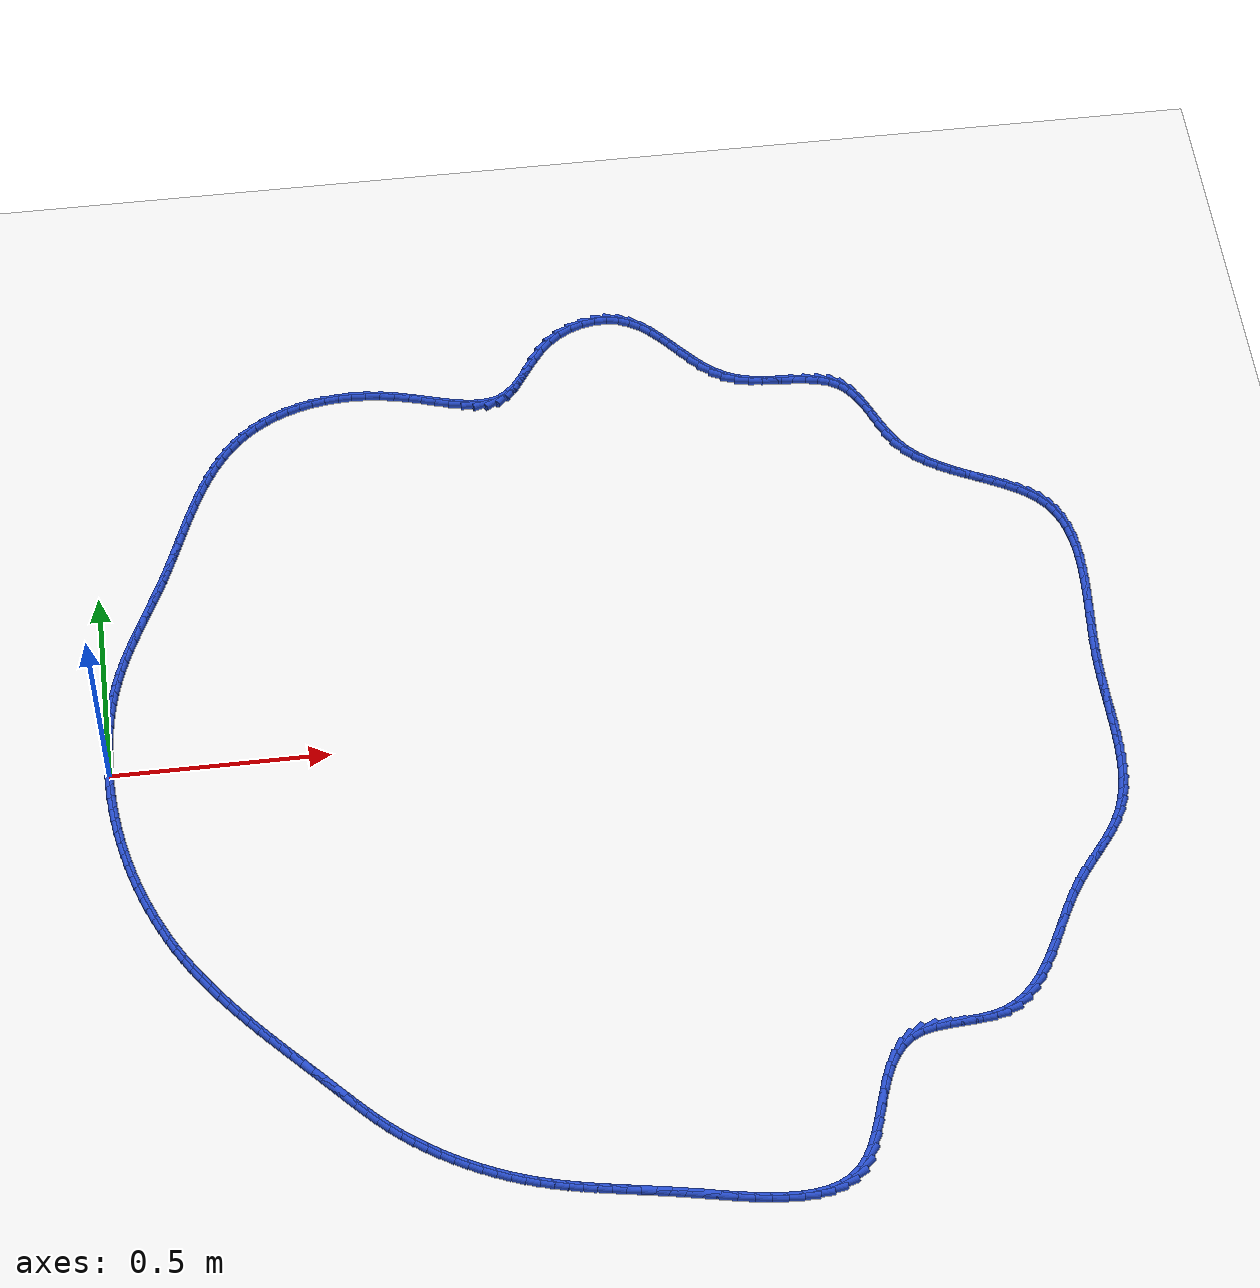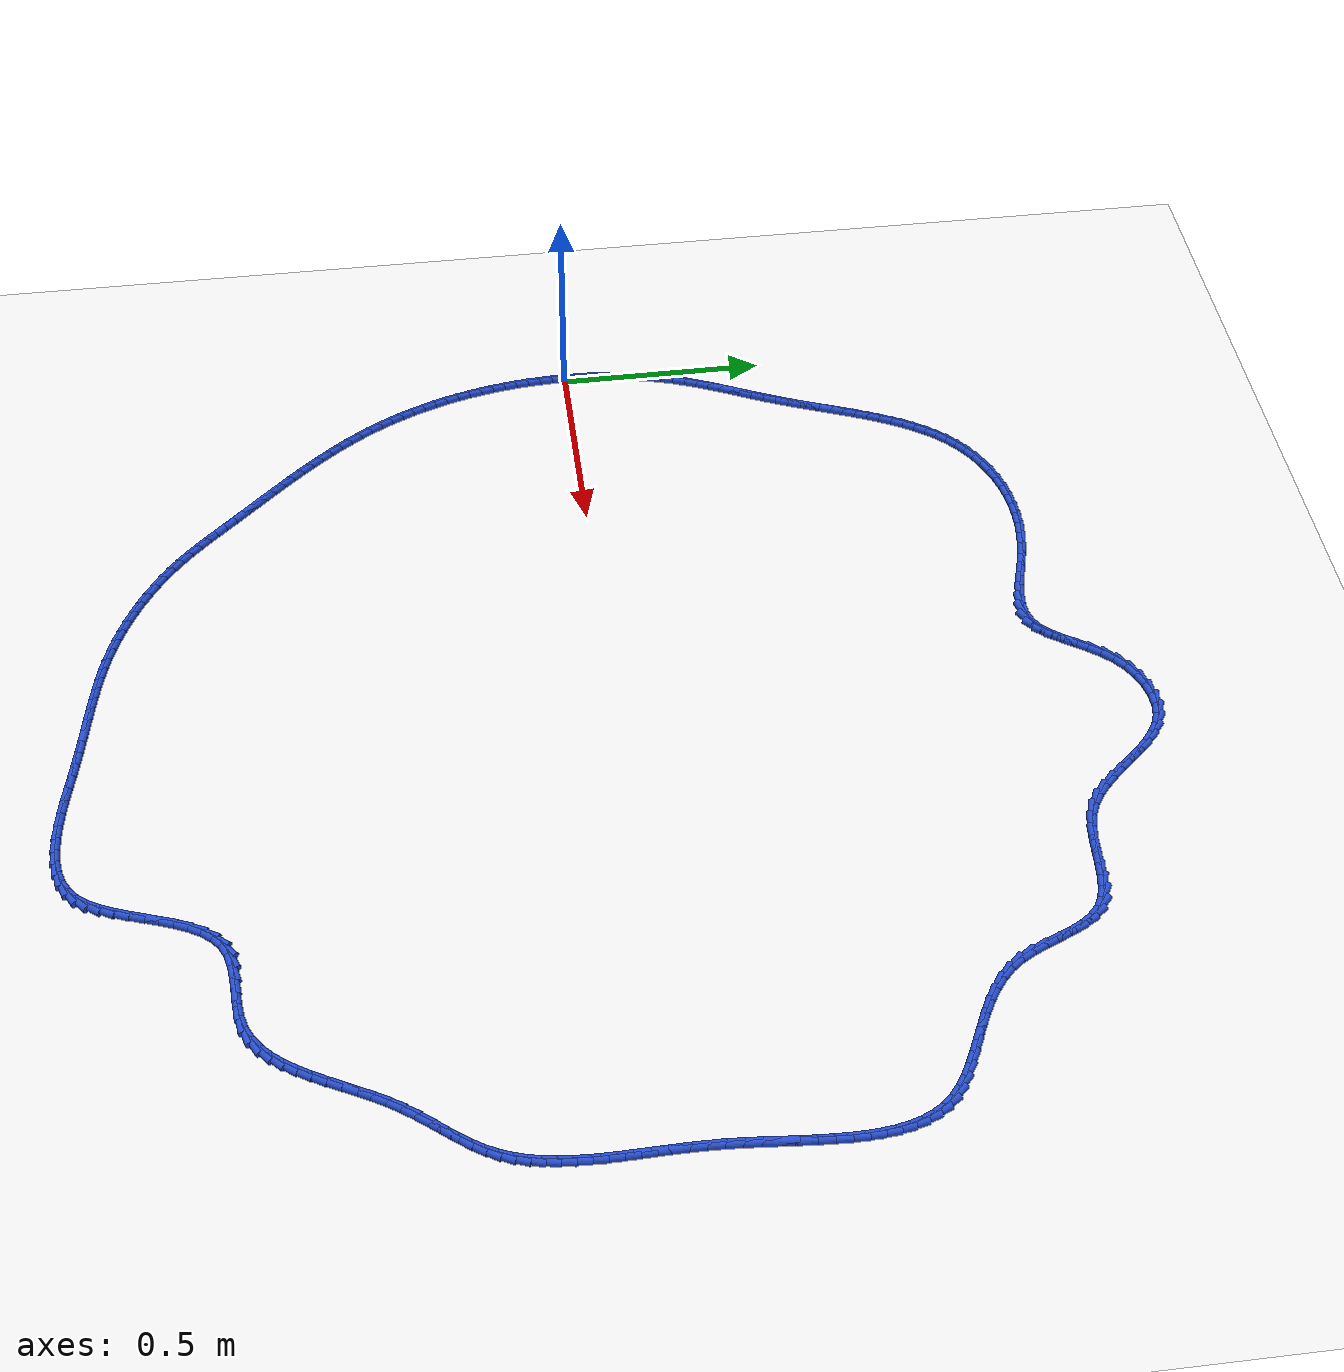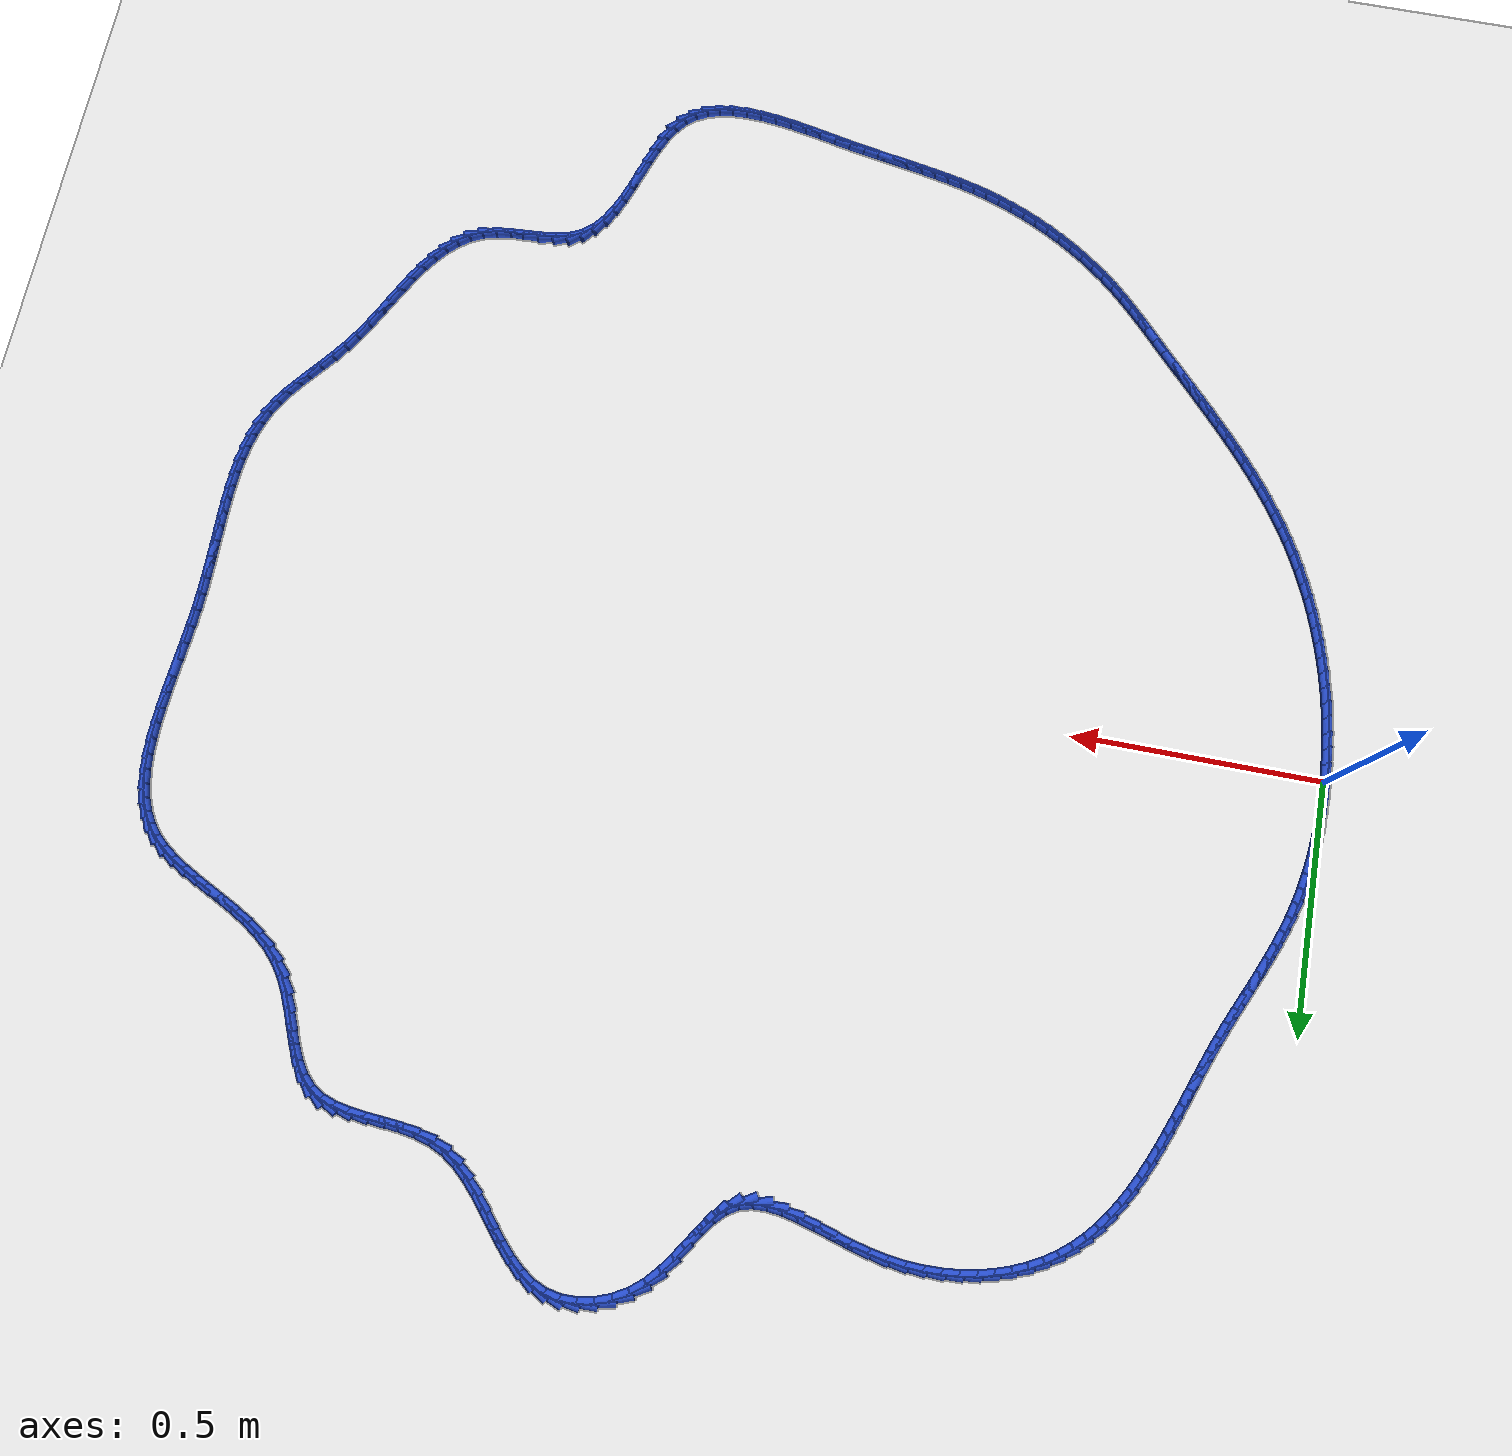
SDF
<sdf version="1.6">
 <world name="default">
  <light name="sun" type="directional">
   <pose>0 0 10 0 -0 0</pose>
   <diffuse>0.8 0.8 0.8 1</diffuse>
   <specular>0.2 0.2 0.2 1</specular>
   <attenuation>
    <range>1000</range>
    <constant>0.9</constant>
    <linear>0.01</linear>
    <quadratic>0.001</quadratic>
   </attenuation>
   <direction>-0.5 0.1 -0.9</direction>
  </light>
  <model name="ground_plane">
   <static>1</static>
   <link name="link">
    <collision name="collision">
     <geometry><plane><normal>0 0 1</normal><size>100 100</size></plane></geometry>
     <surface><friction><ode><mu>100</mu><mu2>50</mu2></ode></friction></surface>
    </collision>
    <visual name="visual">
     <cast_shadows>0</cast_shadows>
     <geometry><plane><normal>0 0 1</normal><size>100 100</size></plane></geometry>
     <material>
      <script><uri>file://media/materials/scripts/gazebo.material</uri><name>Gazebo/WhiteGlow</name></script>
     </material>
    </visual>
   </link>
  </model>
  <gravity>0 0 -9.8</gravity>
  <magnetic_field>6e-06 2.3e-05 -4.2e-05</magnetic_field>
  <atmosphere type="adiabatic"/>
  <physics name="default_physics" default="0" type="ode">
   <max_step_size>0.001</max_step_size>
   <real_time_factor>1</real_time_factor>
   <real_time_update_rate>1000</real_time_update_rate>
  </physics>
  <scene><ambient>0.4 0.4 0.4 1</ambient><background>0.7 0.7 0.7 1</background><shadows>1</shadows></scene>
  <spherical_coordinates>
   <surface_model>EARTH_WGS84</surface_model>
   <latitude_deg>0</latitude_deg>
   <longitude_deg>0</longitude_deg>
   <elevation>0</elevation>
   <heading_deg>0</heading_deg>
  </spherical_coordinates>
  <model name="line">
   <link name="link_0">
    <pose>4.336808689942018e-19 6.938893903907228e-18 0.01 0 1.57 1.5638558301206333</pose>
    <collision name="collision">
     <geometry><cylinder><radius>0.01</radius><length>0.08</length></cylinder></geometry>
    </collision>
    <visual name="visual">
     <material>
      <script><name>Gazebo/Blue</name><uri>file://media/materials/scripts/gazebo.material</uri></script>
     </material>
     <geometry><cylinder><radius>0.01</radius><length>0.08</length></cylinder></geometry>
    </visual>
   </link>
   <link name="link_1">
    <pose>0.00021747084352891172 0.03133311084658414 0.01 0 1.57 1.534074784540277</pose>
    <collision name="collision">
     <geometry><cylinder><radius>0.01</radius><length>0.08</length></cylinder></geometry>
    </collision>
    <visual name="visual">
     <material>
      <script><name>Gazebo/Blue</name><uri>file://media/materials/scripts/gazebo.material</uri></script>
     </material>
     <geometry><cylinder><radius>0.01</radius><length>0.08</length></cylinder></geometry>
    </visual>
   </link>
   <link name="link_2">
    <pose>0.0013689299974788637 0.06267551823842608 0.01 0 1.57 1.5027086300450436</pose>
    <collision name="collision">
     <geometry><cylinder><radius>0.01</radius><length>0.08</length></cylinder></geometry>
    </collision>
    <visual name="visual">
     <material>
      <script><name>Gazebo/Blue</name><uri>file://media/materials/scripts/gazebo.material</uri></script>
     </material>
     <geometry><cylinder><radius>0.01</radius><length>0.08</length></cylinder></geometry>
    </visual>
   </link>
   <link name="link_3">
    <pose>0.0035018581188638992 0.09395328449566563 0.01 0 1.57 1.469603007563532</pose>
    <collision name="collision">
     <geometry><cylinder><radius>0.01</radius><length>0.08</length></cylinder></geometry>
    </collision>
    <visual name="visual">
     <material>
      <script><name>Gazebo/Blue</name><uri>file://media/materials/scripts/gazebo.material</uri></script>
     </material>
     <geometry><cylinder><radius>0.01</radius><length>0.08</length></cylinder></geometry>
    </visual>
   </link>
   <link name="link_4">
    <pose>0.006663735864698064 0.1250924719384425 0.01 0 1.57 1.434600942110471</pose>
    <collision name="collision">
     <geometry><cylinder><radius>0.01</radius><length>0.08</length></cylinder></geometry>
    </collision>
    <visual name="visual">
     <material>
      <script><name>Gazebo/Blue</name><uri>file://media/materials/scripts/gazebo.material</uri></script>
     </material>
     <geometry><cylinder><radius>0.01</radius><length>0.08</length></cylinder></geometry>
    </visual>
   </link>
   <link name="link_5">
    <pose>0.010902043891995394 0.15601914288689644 0.01 0 1.57 1.3975449276549539</pose>
    <collision name="collision">
     <geometry><cylinder><radius>0.01</radius><length>0.08</length></cylinder></geometry>
    </collision>
    <visual name="visual">
     <material>
      <script><name>Gazebo/Blue</name><uri>file://media/materials/scripts/gazebo.material</uri></script>
     </material>
     <geometry><cylinder><radius>0.01</radius><length>0.08</length></cylinder></geometry>
    </visual>
   </link>
   <link name="link_6">
    <pose>0.01626426285776994 0.1866593596611673 0.01 0 1.57 1.358280115290656</pose>
    <collision name="collision">
     <geometry><cylinder><radius>0.01</radius><length>0.08</length></cylinder></geometry>
    </collision>
    <visual name="visual">
     <material>
      <script><name>Gazebo/Blue</name><uri>file://media/materials/scripts/gazebo.material</uri></script>
     </material>
     <geometry><cylinder><radius>0.01</radius><length>0.08</length></cylinder></geometry>
    </visual>
   </link>
   <link name="link_7">
    <pose>0.02279787341903574 0.2169391845813948 0.01 0 1.57 1.3166588308119376</pose>
    <collision name="collision">
     <geometry><cylinder><radius>0.01</radius><length>0.08</length></cylinder></geometry>
    </collision>
    <visual name="visual">
     <material>
      <script><name>Gazebo/Blue</name><uri>file://media/materials/scripts/gazebo.material</uri></script>
     </material>
     <geometry><cylinder><radius>0.01</radius><length>0.08</length></cylinder></geometry>
    </visual>
   </link>
   <link name="link_8">
    <pose>0.03055035623280683 0.24678467996771866 0.01 0 1.57 1.2728599119492168</pose>
    <collision name="collision">
     <geometry><cylinder><radius>0.01</radius><length>0.08</length></cylinder></geometry>
    </collision>
    <visual name="visual">
     <material>
      <script><name>Gazebo/Blue</name><uri>file://media/materials/scripts/gazebo.material</uri></script>
     </material>
     <geometry><cylinder><radius>0.01</radius><length>0.08</length></cylinder></geometry>
    </visual>
   </link>
   <link name="link_9">
    <pose>0.03956111107013749 0.27612834738416225 0.01 0 1.57 1.231723698355262</pose>
    <collision name="collision">
     <geometry><cylinder><radius>0.01</radius><length>0.08</length></cylinder></geometry>
    </collision>
    <visual name="visual">
     <material>
      <script><name>Gazebo/Blue</name><uri>file://media/materials/scripts/gazebo.material</uri></script>
     </material>
     <geometry><cylinder><radius>0.01</radius><length>0.08</length></cylinder></geometry>
    </visual>
   </link>
   <link name="link_10">
    <pose>0.04974472167913721 0.30500214788672947 0.01 0 1.57 1.1973449721834324</pose>
    <collision name="collision">
     <geometry><cylinder><radius>0.01</radius><length>0.08</length></cylinder></geometry>
    </collision>
    <visual name="visual">
     <material>
      <script><name>Gazebo/Blue</name><uri>file://media/materials/scripts/gazebo.material</uri></script>
     </material>
     <geometry><cylinder><radius>0.01</radius><length>0.08</length></cylinder></geometry>
    </visual>
   </link>
   <link name="link_11">
    <pose>0.06091765256214658 0.3335162287298585 0.01 0 1.57 1.1700421164314696</pose>
    <collision name="collision">
     <geometry><cylinder><radius>0.01</radius><length>0.08</length></cylinder></geometry>
    </collision>
    <visual name="visual">
     <material>
      <script><name>Gazebo/Blue</name><uri>file://media/materials/scripts/gazebo.material</uri></script>
     </material>
     <geometry><cylinder><radius>0.01</radius><length>0.08</length></cylinder></geometry>
    </visual>
   </link>
   <link name="link_12">
    <pose>0.07289372381613075 0.3617828443591079 0.01 0 1.57 1.1498981333934843</pose>
    <collision name="collision">
     <geometry><cylinder><radius>0.01</radius><length>0.08</length></cylinder></geometry>
    </collision>
    <visual name="visual">
     <material>
      <script><name>Gazebo/Blue</name><uri>file://media/materials/scripts/gazebo.material</uri></script>
     </material>
     <geometry><cylinder><radius>0.01</radius><length>0.08</length></cylinder></geometry>
    </visual>
   </link>
   <link name="link_13">
    <pose>0.08548675553805478 0.3899142492200359 0.01 0 1.57 1.1369031177951912</pose>
    <collision name="collision">
     <geometry><cylinder><radius>0.01</radius><length>0.08</length></cylinder></geometry>
    </collision>
    <visual name="visual">
     <material>
      <script><name>Gazebo/Blue</name><uri>file://media/materials/scripts/gazebo.material</uri></script>
     </material>
     <geometry><cylinder><radius>0.01</radius><length>0.08</length></cylinder></geometry>
    </visual>
   </link>
   <link name="link_14">
    <pose>0.09851056782488385 0.4180226977582014 0.01 0 1.57 1.1309861143780788</pose>
    <collision name="collision">
     <geometry><cylinder><radius>0.01</radius><length>0.08</length></cylinder></geometry>
    </collision>
    <visual name="visual">
     <material>
      <script><name>Gazebo/Blue</name><uri>file://media/materials/scripts/gazebo.material</uri></script>
     </material>
     <geometry><cylinder><radius>0.01</radius><length>0.08</length></cylinder></geometry>
    </visual>
   </link>
   <link name="link_15">
    <pose>0.11177898077358299 0.4462204444191626 0.01 0 1.57 1.132036569856538</pose>
    <collision name="collision">
     <geometry><cylinder><radius>0.01</radius><length>0.08</length></cylinder></geometry>
    </collision>
    <visual name="visual">
     <material>
      <script><name>Gazebo/Blue</name><uri>file://media/materials/scripts/gazebo.material</uri></script>
     </material>
     <geometry><cylinder><radius>0.01</radius><length>0.08</length></cylinder></geometry>
    </visual>
   </link>
   <link name="link_16">
    <pose>0.12510581448111738 0.47461974364847814 0.01 0 1.57 1.139915007107813</pose>
    <collision name="collision">
     <geometry><cylinder><radius>0.01</radius><length>0.08</length></cylinder></geometry>
    </collision>
    <visual name="visual">
     <material>
      <script><name>Gazebo/Blue</name><uri>file://media/materials/scripts/gazebo.material</uri></script>
     </material>
     <geometry><cylinder><radius>0.01</radius><length>0.08</length></cylinder></geometry>
    </visual>
   </link>
   <link name="link_17">
    <pose>0.1383048890444521 0.5033328498917065 0.01 0 1.57 1.1544536528687406</pose>
    <collision name="collision">
     <geometry><cylinder><radius>0.01</radius><length>0.08</length></cylinder></geometry>
    </collision>
    <visual name="visual">
     <material>
      <script><name>Gazebo/Blue</name><uri>file://media/materials/scripts/gazebo.material</uri></script>
     </material>
     <geometry><cylinder><radius>0.01</radius><length>0.08</length></cylinder></geometry>
    </visual>
   </link>
   <link name="link_18">
    <pose>0.15119002456055225 0.532472017594406 0.01 0 1.57 1.1741188254078128</pose>
    <collision name="collision">
     <geometry><cylinder><radius>0.01</radius><length>0.08</length></cylinder></geometry>
    </collision>
    <visual name="visual">
     <material>
      <script><name>Gazebo/Blue</name><uri>file://media/materials/scripts/gazebo.material</uri></script>
     </material>
     <geometry><cylinder><radius>0.01</radius><length>0.08</length></cylinder></geometry>
    </visual>
   </link>
   <link name="link_19">
    <pose>0.16360969167400757 0.5621215574096162 0.01 0 1.57 1.190258962931134</pose>
    <collision name="collision">
     <geometry><cylinder><radius>0.01</radius><length>0.08</length></cylinder></geometry>
    </collision>
    <visual name="visual">
     <material>
      <script><name>Gazebo/Blue</name><uri>file://media/materials/scripts/gazebo.material</uri></script>
     </material>
     <geometry><cylinder><radius>0.01</radius><length>0.08</length></cylinder></geometry>
    </visual>
   </link>
   <link name="link_20">
    <pose>0.17563624214359053 0.5921852319808181 0.01 0 1.57 1.1996862358167815</pose>
    <collision name="collision">
     <geometry><cylinder><radius>0.01</radius><length>0.08</length></cylinder></geometry>
    </collision>
    <visual name="visual">
     <material>
      <script><name>Gazebo/Blue</name><uri>file://media/materials/scripts/gazebo.material</uri></script>
     </material>
     <geometry><cylinder><radius>0.01</radius><length>0.08</length></cylinder></geometry>
    </visual>
   </link>
   <link name="link_21">
    <pose>0.1874310229001711 0.6224950341586675 0.01 0 1.57 1.2025624499475092</pose>
    <collision name="collision">
     <geometry><cylinder><radius>0.01</radius><length>0.08</length></cylinder></geometry>
    </collision>
    <visual name="visual">
     <material>
      <script><name>Gazebo/Blue</name><uri>file://media/materials/scripts/gazebo.material</uri></script>
     </material>
     <geometry><cylinder><radius>0.01</radius><length>0.08</length></cylinder></geometry>
    </visual>
   </link>
   <link name="link_22">
    <pose>0.19915560765419407 0.652882773908359 0.01 0 1.57 1.198941902530561</pose>
    <collision name="collision">
     <geometry><cylinder><radius>0.01</radius><length>0.08</length></cylinder></geometry>
    </collision>
    <visual name="visual">
     <material>
      <script><name>Gazebo/Blue</name><uri>file://media/materials/scripts/gazebo.material</uri></script>
     </material>
     <geometry><cylinder><radius>0.01</radius><length>0.08</length></cylinder></geometry>
    </visual>
   </link>
   <link name="link_23">
    <pose>0.21097157011610423 0.6831802611950868 0.01 0 1.57 1.1887613834517339</pose>
    <collision name="collision">
     <geometry><cylinder><radius>0.01</radius><length>0.08</length></cylinder></geometry>
    </collision>
    <visual name="visual">
     <material>
      <script><name>Gazebo/Blue</name><uri>file://media/materials/scripts/gazebo.material</uri></script>
     </material>
     <geometry><cylinder><radius>0.01</radius><length>0.08</length></cylinder></geometry>
    </visual>
   </link>
   <link name="link_24">
    <pose>0.22304048399634638 0.7132193059840455 0.01 0 1.57 1.171842120134821</pose>
    <collision name="collision">
     <geometry><cylinder><radius>0.01</radius><length>0.08</length></cylinder></geometry>
    </collision>
    <visual name="visual">
     <material>
      <script><name>Gazebo/Blue</name><uri>file://media/materials/scripts/gazebo.material</uri></script>
     </material>
     <geometry><cylinder><radius>0.01</radius><length>0.08</length></cylinder></geometry>
    </visual>
   </link>
   <link name="link_25">
    <pose>0.2355239230053653 0.7428317182404295 0.01 0 1.57 1.147895903543865</pose>
    <collision name="collision">
     <geometry><cylinder><radius>0.01</radius><length>0.08</length></cylinder></geometry>
    </collision>
    <visual name="visual">
     <material>
      <script><name>Gazebo/Blue</name><uri>file://media/materials/scripts/gazebo.material</uri></script>
     </material>
     <geometry><cylinder><radius>0.01</radius><length>0.08</length></cylinder></geometry>
    </visual>
   </link>
   <link name="link_26">
    <pose>0.24858346085360555 0.7718493079294328 0.01 0 1.57 1.1165381506683605</pose>
    <collision name="collision">
     <geometry><cylinder><radius>0.01</radius><length>0.08</length></cylinder></geometry>
    </collision>
    <visual name="visual">
     <material>
      <script><name>Gazebo/Blue</name><uri>file://media/materials/scripts/gazebo.material</uri></script>
     </material>
     <geometry><cylinder><radius>0.01</radius><length>0.08</length></cylinder></geometry>
    </visual>
   </link>
   <link name="link_27">
    <pose>0.2623806712515122 0.8001038850162505 0.01 0 1.57 1.0773127054481255</pose>
    <collision name="collision">
     <geometry><cylinder><radius>0.01</radius><length>0.08</length></cylinder></geometry>
    </collision>
    <visual name="visual">
     <material>
      <script><name>Gazebo/Blue</name><uri>file://media/materials/scripts/gazebo.material</uri></script>
     </material>
     <geometry><cylinder><radius>0.01</radius><length>0.08</length></cylinder></geometry>
    </visual>
   </link>
   <link name="link_28">
    <pose>0.27707712790952993 0.8274272594660769 0.01 0 1.57 1.029735329368292</pose>
    <collision name="collision">
     <geometry><cylinder><radius>0.01</radius><length>0.08</length></cylinder></geometry>
    </collision>
    <visual name="visual">
     <material>
      <script><name>Gazebo/Blue</name><uri>file://media/materials/scripts/gazebo.material</uri></script>
     </material>
     <geometry><cylinder><radius>0.01</radius><length>0.08</length></cylinder></geometry>
    </visual>
   </link>
   <link name="link_29">
    <pose>0.2928344045381034 0.853651241244106 0.01 0 1.57 0.973364373265339</pose>
    <collision name="collision">
     <geometry><cylinder><radius>0.01</radius><length>0.08</length></cylinder></geometry>
    </collision>
    <visual name="visual">
     <material>
      <script><name>Gazebo/Blue</name><uri>file://media/materials/scripts/gazebo.material</uri></script>
     </material>
     <geometry><cylinder><radius>0.01</radius><length>0.08</length></cylinder></geometry>
    </visual>
   </link>
   <link name="link_30">
    <pose>0.3098140748476775 0.8786076403155323 0.01 0 1.57 0.9079063124235534</pose>
    <collision name="collision">
     <geometry><cylinder><radius>0.01</radius><length>0.08</length></cylinder></geometry>
    </collision>
    <visual name="visual">
     <material>
      <script><name>Gazebo/Blue</name><uri>file://media/materials/scripts/gazebo.material</uri></script>
     </material>
     <geometry><cylinder><radius>0.01</radius><length>0.08</length></cylinder></geometry>
    </visual>
   </link>
   <link name="link_31">
    <pose>0.328177712548697 0.9021282666455503 0.01 0 1.57 0.8333576366759735</pose>
    <collision name="collision">
     <geometry><cylinder><radius>0.01</radius><length>0.08</length></cylinder></geometry>
    </collision>
    <visual name="visual">
     <material>
      <script><name>Gazebo/Blue</name><uri>file://media/materials/scripts/gazebo.material</uri></script>
     </material>
     <geometry><cylinder><radius>0.01</radius><length>0.08</length></cylinder></geometry>
    </visual>
   </link>
   <link name="link_32">
    <pose>0.34808689135160675 0.9240449301993552 0.01 0 1.57 0.7501695802524708</pose>
    <collision name="collision">
     <geometry><cylinder><radius>0.01</radius><length>0.08</length></cylinder></geometry>
    </collision>
    <visual name="visual">
     <material>
      <script><name>Gazebo/Blue</name><uri>file://media/materials/scripts/gazebo.material</uri></script>
     </material>
     <geometry><cylinder><radius>0.01</radius><length>0.08</length></cylinder></geometry>
    </visual>
   </link>
   <link name="link_33">
    <pose>0.3697031849668514 0.9441894409421403 0.01 0 1.57 0.6606928852934253</pose>
    <collision name="collision">
     <geometry><cylinder><radius>0.01</radius><length>0.08</length></cylinder></geometry>
    </collision>
    <visual name="visual">
     <material>
      <script><name>Gazebo/Blue</name><uri>file://media/materials/scripts/gazebo.material</uri></script>
     </material>
     <geometry><cylinder><radius>0.01</radius><length>0.08</length></cylinder></geometry>
    </visual>
   </link>
   <link name="link_34">
    <pose>0.39314694475192513 0.9624103002251032 0.01 0 1.57 0.5723607129313997</pose>
    <collision name="collision">
     <geometry><cylinder><radius>0.01</radius><length>0.08</length></cylinder></geometry>
    </collision>
    <visual name="visual">
     <material>
      <script><name>Gazebo/Blue</name><uri>file://media/materials/scripts/gazebo.material</uri></script>
     </material>
     <geometry><cylinder><radius>0.01</radius><length>0.08</length></cylinder></geometry>
    </visual>
   </link>
   <link name="link_35">
    <pose>0.4183343784347933 0.9786386694097634 0.01 0 1.57 0.4872692908547405</pose>
    <collision name="collision">
     <geometry><cylinder><radius>0.01</radius><length>0.08</length></cylinder></geometry>
    </collision>
    <visual name="visual">
     <material>
      <script><name>Gazebo/Blue</name><uri>file://media/materials/scripts/gazebo.material</uri></script>
     </material>
     <geometry><cylinder><radius>0.01</radius><length>0.08</length></cylinder></geometry>
    </visual>
   </link>
   <link name="link_36">
    <pose>0.4451186144778727 0.9928312513489592 0.01 0 1.57 0.4052853654288564</pose>
    <collision name="collision">
     <geometry><cylinder><radius>0.01</radius><length>0.08</length></cylinder></geometry>
    </collision>
    <visual name="visual">
     <material>
      <script><name>Gazebo/Blue</name><uri>file://media/materials/scripts/gazebo.material</uri></script>
     </material>
     <geometry><cylinder><radius>0.01</radius><length>0.08</length></cylinder></geometry>
    </visual>
   </link>
   <link name="link_37">
    <pose>0.4733527629614037 1.004944756338675 0.01 0 1.57 0.3261747879455871</pose>
    <collision name="collision">
     <geometry><cylinder><radius>0.01</radius><length>0.08</length></cylinder></geometry>
    </collision>
    <visual name="visual">
     <material>
      <script><name>Gazebo/Blue</name><uri>file://media/materials/scripts/gazebo.material</uri></script>
     </material>
     <geometry><cylinder><radius>0.01</radius><length>0.08</length></cylinder></geometry>
    </visual>
   </link>
   <link name="link_38">
    <pose>0.5028899339656265 1.014935894674896 0.01 0 1.57 0.2496388926734102</pose>
    <collision name="collision">
     <geometry><cylinder><radius>0.01</radius><length>0.08</length></cylinder></geometry>
    </collision>
    <visual name="visual">
     <material>
      <script><name>Gazebo/Blue</name><uri>file://media/materials/scripts/gazebo.material</uri></script>
     </material>
     <geometry><cylinder><radius>0.01</radius><length>0.08</length></cylinder></geometry>
    </visual>
   </link>
   <link name="link_39">
    <pose>0.5335832375707819 1.022761376653607 0.01 0 1.57 0.1753441609576724</pose>
    <collision name="collision">
     <geometry><cylinder><radius>0.01</radius><length>0.08</length></cylinder></geometry>
    </collision>
    <visual name="visual">
     <material>
      <script><name>Gazebo/Blue</name><uri>file://media/materials/scripts/gazebo.material</uri></script>
     </material>
     <geometry><cylinder><radius>0.01</radius><length>0.08</length></cylinder></geometry>
    </visual>
   </link>
   <link name="link_40">
    <pose>0.5652857838571095 1.028377912570792 0.01 0 1.57 0.10294541559105572</pose>
    <collision name="collision">
     <geometry><cylinder><radius>0.01</radius><length>0.08</length></cylinder></geometry>
    </collision>
    <visual name="visual">
     <material>
      <script><name>Gazebo/Blue</name><uri>file://media/materials/scripts/gazebo.material</uri></script>
     </material>
     <geometry><cylinder><radius>0.01</radius><length>0.08</length></cylinder></geometry>
    </visual>
   </link>
   <link name="link_41">
    <pose>0.5978506829048502 1.0317422127224363 0.01 0 1.57 0.03210324137186535</pose>
    <collision name="collision">
     <geometry><cylinder><radius>0.01</radius><length>0.08</length></cylinder></geometry>
    </collision>
    <visual name="visual">
     <material>
      <script><name>Gazebo/Blue</name><uri>file://media/materials/scripts/gazebo.material</uri></script>
     </material>
     <geometry><cylinder><radius>0.01</radius><length>0.08</length></cylinder></geometry>
    </visual>
   </link>
   <link name="link_42">
    <pose>0.631131044794244 1.032810987404524 0.01 0 1.57 -0.0375032481259943</pose>
    <collision name="collision">
     <geometry><cylinder><radius>0.01</radius><length>0.08</length></cylinder></geometry>
    </collision>
    <visual name="visual">
     <material>
      <script><name>Gazebo/Blue</name><uri>file://media/materials/scripts/gazebo.material</uri></script>
     </material>
     <geometry><cylinder><radius>0.01</radius><length>0.08</length></cylinder></geometry>
    </visual>
   </link>
   <link name="link_43">
    <pose>0.6649799796055315 1.0315409469130403 0.01 0 1.57 -0.10616713697954354</pose>
    <collision name="collision">
     <geometry><cylinder><radius>0.01</radius><length>0.08</length></cylinder></geometry>
    </collision>
    <visual name="visual">
     <material>
      <script><name>Gazebo/Blue</name><uri>file://media/materials/scripts/gazebo.material</uri></script>
     </material>
     <geometry><cylinder><radius>0.01</radius><length>0.08</length></cylinder></geometry>
    </visual>
   </link>
   <link name="link_44">
    <pose>0.6992505974189523 1.0278888015439693 0.01 0 1.57 -0.17414663860047047</pose>
    <collision name="collision">
     <geometry><cylinder><radius>0.01</radius><length>0.08</length></cylinder></geometry>
    </collision>
    <visual name="visual">
     <material>
      <script><name>Gazebo/Blue</name><uri>file://media/materials/scripts/gazebo.material</uri></script>
     </material>
     <geometry><cylinder><radius>0.01</radius><length>0.08</length></cylinder></geometry>
    </visual>
   </link>
   <link name="link_45">
    <pose>0.7337960062275458 1.0218112722978014 0.01 0 1.57 -0.23589481009776447</pose>
    <collision name="collision">
     <geometry><cylinder><radius>0.01</radius><length>0.08</length></cylinder></geometry>
    </collision>
    <visual name="visual">
     <material>
      <script><name>Gazebo/Blue</name><uri>file://media/materials/scripts/gazebo.material</uri></script>
     </material>
     <geometry><cylinder><radius>0.01</radius><length>0.08</length></cylinder></geometry>
    </visual>
   </link>
   <link name="link_46">
    <pose>0.7684259921887606 1.0134872622041928 0.01 0 1.57 -0.272318202959718</pose>
    <collision name="collision">
     <geometry><cylinder><radius>0.01</radius><length>0.08</length></cylinder></geometry>
    </collision>
    <visual name="visual">
     <material>
      <script><name>Gazebo/Blue</name><uri>file://media/materials/scripts/gazebo.material</uri></script>
     </material>
     <geometry><cylinder><radius>0.01</radius><length>0.08</length></cylinder></geometry>
    </visual>
   </link>
   <link name="link_47">
    <pose>0.8027955850263473 1.003889364079919 0.01 0 1.57 -0.2806275232343057</pose>
    <collision name="collision">
     <geometry><cylinder><radius>0.01</radius><length>0.08</length></cylinder></geometry>
    </collision>
    <visual name="visual">
     <material>
      <script><name>Gazebo/Blue</name><uri>file://media/materials/scripts/gazebo.material</uri></script>
     </material>
     <geometry><cylinder><radius>0.01</radius><length>0.08</length></cylinder></geometry>
    </visual>
   </link>
   <link name="link_48">
    <pose>0.8365252720707271 0.9941673261862982 0.01 0 1.57 -0.25985133850064984</pose>
    <collision name="collision">
     <geometry><cylinder><radius>0.01</radius><length>0.08</length></cylinder></geometry>
    </collision>
    <visual name="visual">
     <material>
      <script><name>Gazebo/Blue</name><uri>file://media/materials/scripts/gazebo.material</uri></script>
     </material>
     <geometry><cylinder><radius>0.01</radius><length>0.08</length></cylinder></geometry>
    </visual>
   </link>
   <link name="link_49">
    <pose>0.8692355406523208 0.9854708967846482 0.01 0 1.57 -0.2053304164187187</pose>
    <collision name="collision">
     <geometry><cylinder><radius>0.01</radius><length>0.08</length></cylinder></geometry>
    </collision>
    <visual name="visual">
     <material>
      <script><name>Gazebo/Blue</name><uri>file://media/materials/scripts/gazebo.material</uri></script>
     </material>
     <geometry><cylinder><radius>0.01</radius><length>0.08</length></cylinder></geometry>
    </visual>
   </link>
   <link name="link_50">
    <pose>0.9005468781015507 0.9789498241362876 0.01 0 1.57 -0.10779772045597241</pose>
    <collision name="collision">
     <geometry><cylinder><radius>0.01</radius><length>0.08</length></cylinder></geometry>
    </collision>
    <visual name="visual">
     <material>
      <script><name>Gazebo/Blue</name><uri>file://media/materials/scripts/gazebo.material</uri></script>
     </material>
     <geometry><cylinder><radius>0.01</radius><length>0.08</length></cylinder></geometry>
    </visual>
   </link>
   <link name="link_51">
    <pose>0.9300797717488367 0.9757538565025338 0.01 0 1.57 0.046683448253966336</pose>
    <collision name="collision">
     <geometry><cylinder><radius>0.01</radius><length>0.08</length></cylinder></geometry>
    </collision>
    <visual name="visual">
     <material>
      <script><name>Gazebo/Blue</name><uri>file://media/materials/scripts/gazebo.material</uri></script>
     </material>
     <geometry><cylinder><radius>0.01</radius><length>0.08</length></cylinder></geometry>
    </visual>
   </link>
   <link name="link_52">
    <pose>0.957454708924601 0.9770327421447049 0.01 0 1.57 0.27110347477854857</pose>
    <collision name="collision">
     <geometry><cylinder><radius>0.01</radius><length>0.08</length></cylinder></geometry>
    </collision>
    <visual name="visual">
     <material>
      <script><name>Gazebo/Blue</name><uri>file://media/materials/scripts/gazebo.material</uri></script>
     </material>
     <geometry><cylinder><radius>0.01</radius><length>0.08</length></cylinder></geometry>
    </visual>
   </link>
   <link name="link_53">
    <pose>0.9822921769592645 0.9839362293241193 0.01 0 1.57 0.5515025662225506</pose>
    <collision name="collision">
     <geometry><cylinder><radius>0.01</radius><length>0.08</length></cylinder></geometry>
    </collision>
    <visual name="visual">
     <material>
      <script><name>Gazebo/Blue</name><uri>file://media/materials/scripts/gazebo.material</uri></script>
     </material>
     <geometry><cylinder><radius>0.01</radius><length>0.08</length></cylinder></geometry>
    </visual>
   </link>
   <link name="link_54">
    <pose>1.0042850126942862 0.9974656610290064 0.01 0 1.57 0.7826459290356425</pose>
    <collision name="collision">
     <geometry><cylinder><radius>0.01</radius><length>0.08</length></cylinder></geometry>
    </collision>
    <visual name="visual">
     <material>
      <script><name>Gazebo/Blue</name><uri>file://media/materials/scripts/gazebo.material</uri></script>
     </material>
     <geometry><cylinder><radius>0.01</radius><length>0.08</length></cylinder></geometry>
    </visual>
   </link>
   <link name="link_55">
    <pose>1.0239203119445939 1.01699317476755 0.01 0 1.57 0.9183010963604974</pose>
    <collision name="collision">
     <geometry><cylinder><radius>0.01</radius><length>0.08</length></cylinder></geometry>
    </collision>
    <visual name="visual">
     <material>
      <script><name>Gazebo/Blue</name><uri>file://media/materials/scripts/gazebo.material</uri></script>
     </material>
     <geometry><cylinder><radius>0.01</radius><length>0.08</length></cylinder></geometry>
    </visual>
   </link>
   <link name="link_56">
    <pose>1.0421762126752507 1.040883669113712 0.01 0 1.57 0.9795146821400785</pose>
    <collision name="collision">
     <geometry><cylinder><radius>0.01</radius><length>0.08</length></cylinder></geometry>
    </collision>
    <visual name="visual">
     <material>
      <script><name>Gazebo/Blue</name><uri>file://media/materials/scripts/gazebo.material</uri></script>
     </material>
     <geometry><cylinder><radius>0.01</radius><length>0.08</length></cylinder></geometry>
    </visual>
   </link>
   <link name="link_57">
    <pose>1.0600381276920652 1.067487120291436 0.01 0 1.57 0.9825663960369981</pose>
    <collision name="collision">
     <geometry><cylinder><radius>0.01</radius><length>0.08</length></cylinder></geometry>
    </collision>
    <visual name="visual">
     <material>
      <script><name>Gazebo/Blue</name><uri>file://media/materials/scripts/gazebo.material</uri></script>
     </material>
     <geometry><cylinder><radius>0.01</radius><length>0.08</length></cylinder></geometry>
    </visual>
   </link>
   <link name="link_58">
    <pose>1.078491469800844 1.0951535045246652 0.01 0 1.57 0.9339287388703186</pose>
    <collision name="collision">
     <geometry><cylinder><radius>0.01</radius><length>0.08</length></cylinder></geometry>
    </collision>
    <visual name="visual">
     <material>
      <script><name>Gazebo/Blue</name><uri>file://media/materials/scripts/gazebo.material</uri></script>
     </material>
     <geometry><cylinder><radius>0.01</radius><length>0.08</length></cylinder></geometry>
    </visual>
   </link>
   <link name="link_59">
    <pose>1.0985216518073955 1.1222327980373437 0.01 0 1.57 0.8327909744610715</pose>
    <collision name="collision">
     <geometry><cylinder><radius>0.01</radius><length>0.08</length></cylinder></geometry>
    </collision>
    <visual name="visual">
     <material>
      <script><name>Gazebo/Blue</name><uri>file://media/materials/scripts/gazebo.material</uri></script>
     </material>
     <geometry><cylinder><radius>0.01</radius><length>0.08</length></cylinder></geometry>
    </visual>
   </link>
   <link name="link_60">
    <pose>1.1211140865175273 1.1470749770534152 0.01 0 1.57 0.6794930536122161</pose>
    <collision name="collision">
     <geometry><cylinder><radius>0.01</radius><length>0.08</length></cylinder></geometry>
    </collision>
    <visual name="visual">
     <material>
      <script><name>Gazebo/Blue</name><uri>file://media/materials/scripts/gazebo.material</uri></script>
     </material>
     <geometry><cylinder><radius>0.01</radius><length>0.08</length></cylinder></geometry>
    </visual>
   </link>
   <link name="link_61">
    <pose>1.1471403100011786 1.1680995658362752 0.01 0 1.57 0.5137155923379565</pose>
    <collision name="collision">
     <geometry><cylinder><radius>0.01</radius><length>0.08</length></cylinder></geometry>
    </collision>
    <visual name="visual">
     <material>
      <script><name>Gazebo/Blue</name><uri>file://media/materials/scripts/gazebo.material</uri></script>
     </material>
     <geometry><cylinder><radius>0.01</radius><length>0.08</length></cylinder></geometry>
    </visual>
   </link>
   <link name="link_62">
    <pose>1.1762054827580577 1.1844995033195724 0.01 0 1.57 0.35469567531681545</pose>
    <collision name="collision">
     <geometry><cylinder><radius>0.01</radius><length>0.08</length></cylinder></geometry>
    </collision>
    <visual name="visual">
     <material>
      <script><name>Gazebo/Blue</name><uri>file://media/materials/scripts/gazebo.material</uri></script>
     </material>
     <geometry><cylinder><radius>0.01</radius><length>0.08</length></cylinder></geometry>
    </visual>
   </link>
   <link name="link_63">
    <pose>1.2071242221961391 1.1959505375174388 0.01 0 1.57 0.1934412882357219</pose>
    <collision name="collision">
     <geometry><cylinder><radius>0.01</radius><length>0.08</length></cylinder></geometry>
    </collision>
    <visual name="visual">
     <material>
      <script><name>Gazebo/Blue</name><uri>file://media/materials/scripts/gazebo.material</uri></script>
     </material>
     <geometry><cylinder><radius>0.01</radius><length>0.08</length></cylinder></geometry>
    </visual>
   </link>
   <link name="link_64">
    <pose>1.2386991099109264 1.2021357670863846 0.01 0 1.57 0.01941275150891111</pose>
    <collision name="collision">
     <geometry><cylinder><radius>0.01</radius><length>0.08</length></cylinder></geometry>
    </collision>
    <visual name="visual">
     <material>
      <script><name>Gazebo/Blue</name><uri>file://media/materials/scripts/gazebo.material</uri></script>
     </material>
     <geometry><cylinder><radius>0.01</radius><length>0.08</length></cylinder></geometry>
    </visual>
   </link>
   <link name="link_65">
    <pose>1.2697327274979264 1.2027382906829194 0.01 0 1.57 -0.17883881847039568</pose>
    <collision name="collision">
     <geometry><cylinder><radius>0.01</radius><length>0.08</length></cylinder></geometry>
    </collision>
    <visual name="visual">
     <material>
      <script><name>Gazebo/Blue</name><uri>file://media/materials/scripts/gazebo.material</uri></script>
     </material>
     <geometry><cylinder><radius>0.01</radius><length>0.08</length></cylinder></geometry>
    </visual>
   </link>
   <link name="link_66">
    <pose>1.2990291138567835 1.197442378517554 0.01 0 1.57 -0.39389775208190275</pose>
    <collision name="collision">
     <geometry><cylinder><radius>0.01</radius><length>0.08</length></cylinder></geometry>
    </collision>
    <visual name="visual">
     <material>
      <script><name>Gazebo/Blue</name><uri>file://media/materials/scripts/gazebo.material</uri></script>
     </material>
     <geometry><cylinder><radius>0.01</radius><length>0.08</length></cylinder></geometry>
    </visual>
   </link>
   <link name="link_67">
    <pose>1.3258457947921805 1.186296867389118 0.01 0 1.57 -0.576917578937118</pose>
    <collision name="collision">
     <geometry><cylinder><radius>0.01</radius><length>0.08</length></cylinder></geometry>
    </collision>
    <visual name="visual">
     <material>
      <script><name>Gazebo/Blue</name><uri>file://media/materials/scripts/gazebo.material</uri></script>
     </material>
     <geometry><cylinder><radius>0.01</radius><length>0.08</length></cylinder></geometry>
    </visual>
   </link>
   <link name="link_68">
    <pose>1.3505344379945867 1.1702301951830496 0.01 0 1.57 -0.7124037963171842</pose>
    <collision name="collision">
     <geometry><cylinder><radius>0.01</radius><length>0.08</length></cylinder></geometry>
    </collision>
    <visual name="visual">
     <material>
      <script><name>Gazebo/Blue</name><uri>file://media/materials/scripts/gazebo.material</uri></script>
     </material>
     <geometry><cylinder><radius>0.01</radius><length>0.08</length></cylinder></geometry>
    </visual>
   </link>
   <link name="link_69">
    <pose>1.3736084221562475 1.150300802277817 0.01 0 1.57 -0.8024180156804753</pose>
    <collision name="collision">
     <geometry><cylinder><radius>0.01</radius><length>0.08</length></cylinder></geometry>
    </collision>
    <visual name="visual">
     <material>
      <script><name>Gazebo/Blue</name><uri>file://media/materials/scripts/gazebo.material</uri></script>
     </material>
     <geometry><cylinder><radius>0.01</radius><length>0.08</length></cylinder></geometry>
    </visual>
   </link>
   <link name="link_70">
    <pose>1.3955811259694093 1.127567129051889 0.01 0 1.57 -0.852771395001808</pose>
    <collision name="collision">
     <geometry><cylinder><radius>0.01</radius><length>0.08</length></cylinder></geometry>
    </collision>
    <visual name="visual">
     <material>
      <script><name>Gazebo/Blue</name><uri>file://media/materials/scripts/gazebo.material</uri></script>
     </material>
     <geometry><cylinder><radius>0.01</radius><length>0.08</length></cylinder></geometry>
    </visual>
   </link>
   <link name="link_71">
    <pose>1.4169659281263167 1.1030876158837333 0.01 0 1.57 -0.868187551532088</pose>
    <collision name="collision">
     <geometry><cylinder><radius>0.01</radius><length>0.08</length></cylinder></geometry>
    </collision>
    <visual name="visual">
     <material>
      <script><name>Gazebo/Blue</name><uri>file://media/materials/scripts/gazebo.material</uri></script>
     </material>
     <geometry><cylinder><radius>0.01</radius><length>0.08</length></cylinder></geometry>
    </visual>
   </link>
   <link name="link_72">
    <pose>1.4382762073192166 1.0779207031518199 0.01 0 1.57 -0.850762782956271</pose>
    <collision name="collision">
     <geometry><cylinder><radius>0.01</radius><length>0.08</length></cylinder></geometry>
    </collision>
    <visual name="visual">
     <material>
      <script><name>Gazebo/Blue</name><uri>file://media/materials/scripts/gazebo.material</uri></script>
     </material>
     <geometry><cylinder><radius>0.01</radius><length>0.08</length></cylinder></geometry>
    </visual>
   </link>
   <link name="link_73">
    <pose>1.4600253422403542 1.0531248312346158 0.01 0 1.57 -0.79983288287618</pose>
    <collision name="collision">
     <geometry><cylinder><radius>0.01</radius><length>0.08</length></cylinder></geometry>
    </collision>
    <visual name="visual">
     <material>
      <script><name>Gazebo/Blue</name><uri>file://media/materials/scripts/gazebo.material</uri></script>
     </material>
     <geometry><cylinder><radius>0.01</radius><length>0.08</length></cylinder></geometry>
    </visual>
   </link>
   <link name="link_74">
    <pose>1.4827267115819764 1.0297584405105893 0.01 0 1.57 -0.7125231092848645</pose>
    <collision name="collision">
     <geometry><cylinder><radius>0.01</radius><length>0.08</length></cylinder></geometry>
    </collision>
    <visual name="visual">
     <material>
      <script><name>Gazebo/Blue</name><uri>file://media/materials/scripts/gazebo.material</uri></script>
     </material>
     <geometry><cylinder><radius>0.01</radius><length>0.08</length></cylinder></geometry>
    </visual>
   </link>
   <link name="link_75">
    <pose>1.5068936940363278 1.0088799713582102 0.01 0 1.57 -0.585388804675232</pose>
    <collision name="collision">
     <geometry><cylinder><radius>0.01</radius><length>0.08</length></cylinder></geometry>
    </collision>
    <visual name="visual">
     <material>
      <script><name>Gazebo/Blue</name><uri>file://media/materials/scripts/gazebo.material</uri></script>
     </material>
     <geometry><cylinder><radius>0.01</radius><length>0.08</length></cylinder></geometry>
    </visual>
   </link>
   <link name="link_76">
    <pose>1.5330396682956549 0.9915478641559462 0.01 0 1.57 -0.4194120932250192</pose>
    <collision name="collision">
     <geometry><cylinder><radius>0.01</radius><length>0.08</length></cylinder></geometry>
    </collision>
    <visual name="visual">
     <material>
      <script><name>Gazebo/Blue</name><uri>file://media/materials/scripts/gazebo.material</uri></script>
     </material>
     <geometry><cylinder><radius>0.01</radius><length>0.08</length></cylinder></geometry>
    </visual>
   </link>
   <link name="link_77">
    <pose>1.5616590536586246 0.9787874080629291 0.01 0 1.57 -0.2593375815803751</pose>
    <collision name="collision">
     <geometry><cylinder><radius>0.01</radius><length>0.08</length></cylinder></geometry>
    </collision>
    <visual name="visual">
     <material>
      <script><name>Gazebo/Blue</name><uri>file://media/materials/scripts/gazebo.material</uri></script>
     </material>
     <geometry><cylinder><radius>0.01</radius><length>0.08</length></cylinder></geometry>
    </visual>
   </link>
   <link name="link_78">
    <pose>1.5926419726446042 0.9705672563816908 0.01 0 1.57 -0.15143713851932095</pose>
    <collision name="collision">
     <geometry><cylinder><radius>0.01</radius><length>0.08</length></cylinder></geometry>
    </collision>
    <visual name="visual">
     <material>
      <script><name>Gazebo/Blue</name><uri>file://media/materials/scripts/gazebo.material</uri></script>
     </material>
     <geometry><cylinder><radius>0.01</radius><length>0.08</length></cylinder></geometry>
    </visual>
   </link>
   <link name="link_79">
    <pose>1.6251627205069497 0.9656044112686553 0.01 0 1.57 -0.09196378979248848</pose>
    <collision name="collision">
     <geometry><cylinder><radius>0.01</radius><length>0.08</length></cylinder></geometry>
    </collision>
    <visual name="visual">
     <material>
      <script><name>Gazebo/Blue</name><uri>file://media/materials/scripts/gazebo.material</uri></script>
     </material>
     <geometry><cylinder><radius>0.01</radius><length>0.08</length></cylinder></geometry>
    </visual>
   </link>
   <link name="link_80">
    <pose>1.6583541262209462 0.9625433695190554 0.01 0 1.57 -0.07606902193979613</pose>
    <collision name="collision">
     <geometry><cylinder><radius>0.01</radius><length>0.08</length></cylinder></geometry>
    </collision>
    <visual name="visual">
     <material>
      <script><name>Gazebo/Blue</name><uri>file://media/materials/scripts/gazebo.material</uri></script>
     </material>
     <geometry><cylinder><radius>0.01</radius><length>0.08</length></cylinder></geometry>
    </visual>
   </link>
   <link name="link_81">
    <pose>1.69134901876188 0.9600286279281255 0.01 0 1.57 -0.10372347198887674</pose>
    <collision name="collision">
     <geometry><cylinder><radius>0.01</radius><length>0.08</length></cylinder></geometry>
    </collision>
    <visual name="visual">
     <material>
      <script><name>Gazebo/Blue</name><uri>file://media/materials/scripts/gazebo.material</uri></script>
     </material>
     <geometry><cylinder><radius>0.01</radius><length>0.08</length></cylinder></geometry>
    </visual>
   </link>
   <link name="link_82">
    <pose>1.723280227105036 0.9567046832910988 0.01 0 1.57 -0.18095166411996252</pose>
    <collision name="collision">
     <geometry><cylinder><radius>0.01</radius><length>0.08</length></cylinder></geometry>
    </collision>
    <visual name="visual">
     <material>
      <script><name>Gazebo/Blue</name><uri>file://media/materials/scripts/gazebo.material</uri></script>
     </material>
     <geometry><cylinder><radius>0.01</radius><length>0.08</length></cylinder></geometry>
    </visual>
   </link>
   <link name="link_83">
    <pose>1.7532805802257003 0.9512160324032101 0.01 0 1.57 -0.319811096342936</pose>
    <collision name="collision">
     <geometry><cylinder><radius>0.01</radius><length>0.08</length></cylinder></geometry>
    </collision>
    <visual name="visual">
     <material>
      <script><name>Gazebo/Blue</name><uri>file://media/materials/scripts/gazebo.material</uri></script>
     </material>
     <geometry><cylinder><radius>0.01</radius><length>0.08</length></cylinder></geometry>
    </visual>
   </link>
   <link name="link_84">
    <pose>1.780482907099159 0.9422071720596927 0.01 0 1.57 -0.5329211066232714</pose>
    <collision name="collision">
     <geometry><cylinder><radius>0.01</radius><length>0.08</length></cylinder></geometry>
    </collision>
    <visual name="visual">
     <material>
      <script><name>Gazebo/Blue</name><uri>file://media/materials/scripts/gazebo.material</uri></script>
     </material>
     <geometry><cylinder><radius>0.01</radius><length>0.08</length></cylinder></geometry>
    </visual>
   </link>
   <link name="link_85">
    <pose>1.8040206808023926 0.9283234710823451 0.01 0 1.57 -0.786267947462315</pose>
    <collision name="collision">
     <geometry><cylinder><radius>0.01</radius><length>0.08</length></cylinder></geometry>
    </collision>
    <visual name="visual">
     <material>
      <script><name>Gazebo/Blue</name><uri>file://media/materials/scripts/gazebo.material</uri></script>
     </material>
     <geometry><cylinder><radius>0.01</radius><length>0.08</length></cylinder></geometry>
    </visual>
   </link>
   <link name="link_86">
    <pose>1.8234830478301578 0.9088272184594736 0.01 0 1.57 -0.9790093792275554</pose>
    <collision name="collision">
     <geometry><cylinder><radius>0.01</radius><length>0.08</length></cylinder></geometry>
    </collision>
    <visual name="visual">
     <material>
      <script><name>Gazebo/Blue</name><uri>file://media/materials/scripts/gazebo.material</uri></script>
     </material>
     <geometry><cylinder><radius>0.01</radius><length>0.08</length></cylinder></geometry>
    </visual>
   </link>
   <link name="link_87">
    <pose>1.8397138932869133 0.8846794495223201 0.01 0 1.57 -1.098960619112175</pose>
    <collision name="collision">
     <geometry><cylinder><radius>0.01</radius><length>0.08</length></cylinder></geometry>
    </collision>
    <visual name="visual">
     <material>
      <script><name>Gazebo/Blue</name><uri>file://media/materials/scripts/gazebo.material</uri></script>
     </material>
     <geometry><cylinder><radius>0.01</radius><length>0.08</length></cylinder></geometry>
    </visual>
   </link>
   <link name="link_88">
    <pose>1.853771208993774 0.8571310711332232 0.01 0 1.57 -1.159831938851119</pose>
    <collision name="collision">
     <geometry><cylinder><radius>0.01</radius><length>0.08</length></cylinder></geometry>
    </collision>
    <visual name="visual">
     <material>
      <script><name>Gazebo/Blue</name><uri>file://media/materials/scripts/gazebo.material</uri></script>
     </material>
     <geometry><cylinder><radius>0.01</radius><length>0.08</length></cylinder></geometry>
    </visual>
   </link>
   <link name="link_89">
    <pose>1.8667129867718557 0.8274329901545214 0.01 0 1.57 -1.1722367865172105</pose>
    <collision name="collision">
     <geometry><cylinder><radius>0.01</radius><length>0.08</length></cylinder></geometry>
    </collision>
    <visual name="visual">
     <material>
      <script><name>Gazebo/Blue</name><uri>file://media/materials/scripts/gazebo.material</uri></script>
     </material>
     <geometry><cylinder><radius>0.01</radius><length>0.08</length></cylinder></geometry>
    </visual>
   </link>
   <link name="link_90">
    <pose>1.8795972184422751 0.7968361134485545 0.01 0 1.57 -1.140419624426863</pose>
    <collision name="collision">
     <geometry><cylinder><radius>0.01</radius><length>0.08</length></cylinder></geometry>
    </collision>
    <visual name="visual">
     <material>
      <script><name>Gazebo/Blue</name><uri>file://media/materials/scripts/gazebo.material</uri></script>
     </material>
     <geometry><cylinder><radius>0.01</radius><length>0.08</length></cylinder></geometry>
    </visual>
   </link>
   <link name="link_91">
    <pose>1.8934818958261475 0.7665913478776608 0.01 0 1.57 -1.0628702563807881</pose>
    <collision name="collision">
     <geometry><cylinder><radius>0.01</radius><length>0.08</length></cylinder></geometry>
    </collision>
    <visual name="visual">
     <material>
      <script><name>Gazebo/Blue</name><uri>file://media/materials/scripts/gazebo.material</uri></script>
     </material>
     <geometry><cylinder><radius>0.01</radius><length>0.08</length></cylinder></geometry>
    </visual>
   </link>
   <link name="link_92">
    <pose>1.9094250107445885 0.7379496003041794 0.01 0 1.57 -0.9362865586724899</pose>
    <collision name="collision">
     <geometry><cylinder><radius>0.01</radius><length>0.08</length></cylinder></geometry>
    </collision>
    <visual name="visual">
     <material>
      <script><name>Gazebo/Blue</name><uri>file://media/materials/scripts/gazebo.material</uri></script>
     </material>
     <geometry><cylinder><radius>0.01</radius><length>0.08</length></cylinder></geometry>
    </visual>
   </link>
   <link name="link_93">
    <pose>1.9284400900815828 0.7121154658395582 0.01 0 1.57 -0.7954403564444568</pose>
    <collision name="collision">
     <geometry><cylinder><radius>0.01</radius><length>0.08</length></cylinder></geometry>
    </collision>
    <visual name="visual">
     <material>
      <script><name>Gazebo/Blue</name><uri>file://media/materials/scripts/gazebo.material</uri></script>
     </material>
     <geometry><cylinder><radius>0.01</radius><length>0.08</length></cylinder></geometry>
    </visual>
   </link>
   <link name="link_94">
    <pose>1.9506931934258969 0.689410873458822 0.01 0 1.57 -0.6778523167720722</pose>
    <collision name="collision">
     <geometry><cylinder><radius>0.01</radius><length>0.08</length></cylinder></geometry>
    </collision>
    <visual name="visual">
     <material>
      <script><name>Gazebo/Blue</name><uri>file://media/materials/scripts/gazebo.material</uri></script>
     </material>
     <geometry><cylinder><radius>0.01</radius><length>0.08</length></cylinder></geometry>
    </visual>
   </link>
   <link name="link_95">
    <pose>1.9755901521543922 0.6693659484858223 0.01 0 1.57 -0.5863740071048473</pose>
    <collision name="collision">
     <geometry><cylinder><radius>0.01</radius><length>0.08</length></cylinder></geometry>
    </collision>
    <visual name="visual">
     <material>
      <script><name>Gazebo/Blue</name><uri>file://media/materials/scripts/gazebo.material</uri></script>
     </material>
     <geometry><cylinder><radius>0.01</radius><length>0.08</length></cylinder></geometry>
    </visual>
   </link>
   <link name="link_96">
    <pose>2.00250984509618 0.6514827442452616 0.01 0 1.57 -0.5200992182691503</pose>
    <collision name="collision">
     <geometry><cylinder><radius>0.01</radius><length>0.08</length></cylinder></geometry>
    </collision>
    <visual name="visual">
     <material>
      <script><name>Gazebo/Blue</name><uri>file://media/materials/scripts/gazebo.material</uri></script>
     </material>
     <geometry><cylinder><radius>0.01</radius><length>0.08</length></cylinder></geometry>
    </visual>
   </link>
   <link name="link_97">
    <pose>2.0308311510803705 0.6352633140618433 0.01 0 1.57 -0.47737110170168484</pose>
    <collision name="collision">
     <geometry><cylinder><radius>0.01</radius><length>0.08</length></cylinder></geometry>
    </collision>
    <visual name="visual">
     <material>
      <script><name>Gazebo/Blue</name><uri>file://media/materials/scripts/gazebo.material</uri></script>
     </material>
     <geometry><cylinder><radius>0.01</radius><length>0.08</length></cylinder></geometry>
    </visual>
   </link>
   <link name="link_98">
    <pose>2.059932948936073 0.6202097112602699 0.01 0 1.57 -0.45693069722691027</pose>
    <collision name="collision">
     <geometry><cylinder><radius>0.01</radius><length>0.08</length></cylinder></geometry>
    </collision>
    <visual name="visual">
     <material>
      <script><name>Gazebo/Blue</name><uri>file://media/materials/scripts/gazebo.material</uri></script>
     </material>
     <geometry><cylinder><radius>0.01</radius><length>0.08</length></cylinder></geometry>
    </visual>
   </link>
   <link name="link_99">
    <pose>2.0891941174924 0.6058239891652442 0.01 0 1.57 -0.4585255500110028</pose>
    <collision name="collision">
     <geometry><cylinder><radius>0.01</radius><length>0.08</length></cylinder></geometry>
    </collision>
    <visual name="visual">
     <material>
      <script><name>Gazebo/Blue</name><uri>file://media/materials/scripts/gazebo.material</uri></script>
     </material>
     <geometry><cylinder><radius>0.01</radius><length>0.08</length></cylinder></geometry>
    </visual>
   </link>
   <link name="link_100">
    <pose>2.117993535578461 0.5916082011014687 0.01 0 1.57 -0.4832380694866959</pose>
    <collision name="collision">
     <geometry><cylinder><radius>0.01</radius><length>0.08</length></cylinder></geometry>
    </collision>
    <visual name="visual">
     <material>
      <script><name>Gazebo/Blue</name><uri>file://media/materials/scripts/gazebo.material</uri></script>
     </material>
     <geometry><cylinder><radius>0.01</radius><length>0.08</length></cylinder></geometry>
    </visual>
   </link>
   <link name="link_101">
    <pose>2.1457100820233674 0.577064400393647 0.01 0 1.57 -0.5336713087816723</pose>
    <collision name="collision">
     <geometry><cylinder><radius>0.01</radius><length>0.08</length></cylinder></geometry>
    </collision>
    <visual name="visual">
     <material>
      <script><name>Gazebo/Blue</name><uri>file://media/materials/scripts/gazebo.material</uri></script>
     </material>
     <geometry><cylinder><radius>0.01</radius><length>0.08</length></cylinder></geometry>
    </visual>
   </link>
   <link name="link_102">
    <pose>2.17172263565623 0.5616946403664816 0.01 0 1.57 -0.6139051651730468</pose>
    <collision name="collision">
     <geometry><cylinder><radius>0.01</radius><length>0.08</length></cylinder></geometry>
    </collision>
    <visual name="visual">
     <material>
      <script><name>Gazebo/Blue</name><uri>file://media/materials/scripts/gazebo.material</uri></script>
     </material>
     <geometry><cylinder><radius>0.01</radius><length>0.08</length></cylinder></geometry>
    </visual>
   </link>
   <link name="link_103">
    <pose>2.195410075306157 0.5450009743446751 0.01 0 1.57 -0.7287631346408664</pose>
    <collision name="collision">
     <geometry><cylinder><radius>0.01</radius><length>0.08</length></cylinder></geometry>
    </collision>
    <visual name="visual">
     <material>
      <script><name>Gazebo/Blue</name><uri>file://media/materials/scripts/gazebo.material</uri></script>
     </material>
     <geometry><cylinder><radius>0.01</radius><length>0.08</length></cylinder></geometry>
    </visual>
   </link>
   <link name="link_104">
    <pose>2.2161512798022627 0.5264854556529301 0.01 0 1.57 -0.8764051815039844</pose>
    <collision name="collision">
     <geometry><cylinder><radius>0.01</radius><length>0.08</length></cylinder></geometry>
    </collision>
    <visual name="visual">
     <material>
      <script><name>Gazebo/Blue</name><uri>file://media/materials/scripts/gazebo.material</uri></script>
     </material>
     <geometry><cylinder><radius>0.01</radius><length>0.08</length></cylinder></geometry>
    </visual>
   </link>
   <link name="link_105">
    <pose>2.233434888441509 0.5057304799783171 0.01 0 1.57 -1.0258224913205392</pose>
    <collision name="collision">
     <geometry><cylinder><radius>0.01</radius><length>0.08</length></cylinder></geometry>
    </collision>
    <visual name="visual">
     <material>
      <script><name>Gazebo/Blue</name><uri>file://media/materials/scripts/gazebo.material</uri></script>
     </material>
     <geometry><cylinder><radius>0.01</radius><length>0.08</length></cylinder></geometry>
    </visual>
   </link>
   <link name="link_106">
    <pose>2.247357672190513 0.48276358264629077 0.01 0 1.57 -1.1606868679581817</pose>
    <collision name="collision">
     <geometry><cylinder><radius>0.01</radius><length>0.08</length></cylinder></geometry>
    </collision>
    <visual name="visual">
     <material>
      <script><name>Gazebo/Blue</name><uri>file://media/materials/scripts/gazebo.material</uri></script>
     </material>
     <geometry><cylinder><radius>0.01</radius><length>0.08</length></cylinder></geometry>
    </visual>
   </link>
   <link name="link_107">
    <pose>2.2582258304452822 0.457765596203913 0.01 0 1.57 -1.2771029647505892</pose>
    <collision name="collision">
     <geometry><cylinder><radius>0.01</radius><length>0.08</length></cylinder></geometry>
    </collision>
    <visual name="visual">
     <material>
      <script><name>Gazebo/Blue</name><uri>file://media/materials/scripts/gazebo.material</uri></script>
     </material>
     <geometry><cylinder><radius>0.01</radius><length>0.08</length></cylinder></geometry>
    </visual>
   </link>
   <link name="link_108">
    <pose>2.2663457566625778 0.43091749524664824 0.01 0 1.57 -1.374256014430007</pose>
    <collision name="collision">
     <geometry><cylinder><radius>0.01</radius><length>0.08</length></cylinder></geometry>
    </collision>
    <visual name="visual">
     <material>
      <script><name>Gazebo/Blue</name><uri>file://media/materials/scripts/gazebo.material</uri></script>
     </material>
     <geometry><cylinder><radius>0.01</radius><length>0.08</length></cylinder></geometry>
    </visual>
   </link>
   <link name="link_109">
    <pose>2.272023844299159 0.40240025436996174 0.01 0 1.57 -1.4532735842693072</pose>
    <collision name="collision">
     <geometry><cylinder><radius>0.01</radius><length>0.08</length></cylinder></geometry>
    </collision>
    <visual name="visual">
     <material>
      <script><name>Gazebo/Blue</name><uri>file://media/materials/scripts/gazebo.material</uri></script>
     </material>
     <geometry><cylinder><radius>0.01</radius><length>0.08</length></cylinder></geometry>
    </visual>
   </link>
   <link name="link_110">
    <pose>2.275566486811786 0.37239484816931806 0.01 0 1.57 -1.5161255735686605</pose>
    <collision name="collision">
     <geometry><cylinder><radius>0.01</radius><length>0.08</length></cylinder></geometry>
    </collision>
    <visual name="visual">
     <material>
      <script><name>Gazebo/Blue</name><uri>file://media/materials/scripts/gazebo.material</uri></script>
     </material>
     <geometry><cylinder><radius>0.01</radius><length>0.08</length></cylinder></geometry>
    </visual>
   </link>
   <link name="link_111">
    <pose>2.277280077657219 0.34108225124018204 0.01 0 1.57 -1.5649104631605804</pose>
    <collision name="collision">
     <geometry><cylinder><radius>0.01</radius><length>0.08</length></cylinder></geometry>
    </collision>
    <visual name="visual">
     <material>
      <script><name>Gazebo/Blue</name><uri>file://media/materials/scripts/gazebo.material</uri></script>
     </material>
     <geometry><cylinder><radius>0.01</radius><length>0.08</length></cylinder></geometry>
    </visual>
   </link>
   <link name="link_112">
    <pose>2.2774710102922184 0.3086434381780177 0.01 0 1.57 1.5400927494768115</pose>
    <collision name="collision">
     <geometry><cylinder><radius>0.01</radius><length>0.08</length></cylinder></geometry>
    </collision>
    <visual name="visual">
     <material>
      <script><name>Gazebo/Blue</name><uri>file://media/materials/scripts/gazebo.material</uri></script>
     </material>
     <geometry><cylinder><radius>0.01</radius><length>0.08</length></cylinder></geometry>
    </visual>
   </link>
   <link name="link_113">
    <pose>2.2764456781735425 0.2752593835782909 0.01 0 1.57 1.5141863487807568</pose>
    <collision name="collision">
     <geometry><cylinder><radius>0.01</radius><length>0.08</length></cylinder></geometry>
    </collision>
    <visual name="visual">
     <material>
      <script><name>Gazebo/Blue</name><uri>file://media/materials/scripts/gazebo.material</uri></script>
     </material>
     <geometry><cylinder><radius>0.01</radius><length>0.08</length></cylinder></geometry>
    </visual>
   </link>
   <link name="link_114">
    <pose>2.2745104747579536 0.24111106203646582 0.01 0 1.57 1.4978318366877614</pose>
    <collision name="collision">
     <geometry><cylinder><radius>0.01</radius><length>0.08</length></cylinder></geometry>
    </collision>
    <visual name="visual">
     <material>
      <script><name>Gazebo/Blue</name><uri>file://media/materials/scripts/gazebo.material</uri></script>
     </material>
     <geometry><cylinder><radius>0.01</radius><length>0.08</length></cylinder></geometry>
    </visual>
   </link>
   <link name="link_115">
    <pose>2.2719717935022103 0.20637944814800663 0.01 0 1.57 1.4902578981511396</pose>
    <collision name="collision">
     <geometry><cylinder><radius>0.01</radius><length>0.08</length></cylinder></geometry>
    </collision>
    <visual name="visual">
     <material>
      <script><name>Gazebo/Blue</name><uri>file://media/materials/scripts/gazebo.material</uri></script>
     </material>
     <geometry><cylinder><radius>0.01</radius><length>0.08</length></cylinder></geometry>
    </visual>
   </link>
   <link name="link_116">
    <pose>2.269136027863073 0.1712455165083792 0.01 0 1.57 1.4910215783226872</pose>
    <collision name="collision">
     <geometry><cylinder><radius>0.01</radius><length>0.08</length></cylinder></geometry>
    </collision>
    <visual name="visual">
     <material>
      <script><name>Gazebo/Blue</name><uri>file://media/materials/scripts/gazebo.material</uri></script>
     </material>
     <geometry><cylinder><radius>0.01</radius><length>0.08</length></cylinder></geometry>
    </visual>
   </link>
   <link name="link_117">
    <pose>2.266309571297301 0.1358902417130476 0.01 0 1.57 1.499980955081295</pose>
    <collision name="collision">
     <geometry><cylinder><radius>0.01</radius><length>0.08</length></cylinder></geometry>
    </collision>
    <visual name="visual">
     <material>
      <script><name>Gazebo/Blue</name><uri>file://media/materials/scripts/gazebo.material</uri></script>
     </material>
     <geometry><cylinder><radius>0.01</radius><length>0.08</length></cylinder></geometry>
    </visual>
   </link>
   <link name="link_118">
    <pose>2.2637988172616557 0.10049459835747668 0.01 0 1.57 1.517276190273626</pose>
    <collision name="collision">
     <geometry><cylinder><radius>0.01</radius><length>0.08</length></cylinder></geometry>
    </collision>
    <visual name="visual">
     <material>
      <script><name>Gazebo/Blue</name><uri>file://media/materials/scripts/gazebo.material</uri></script>
     </material>
     <geometry><cylinder><radius>0.01</radius><length>0.08</length></cylinder></geometry>
    </visual>
   </link>
   <link name="link_119">
    <pose>2.2619101592128956 0.06523956103713069 0.01 0 1.57 1.542447162731856</pose>
    <collision name="collision">
     <geometry><cylinder><radius>0.01</radius><length>0.08</length></cylinder></geometry>
    </collision>
    <visual name="visual">
     <material>
      <script><name>Gazebo/Blue</name><uri>file://media/materials/scripts/gazebo.material</uri></script>
     </material>
     <geometry><cylinder><radius>0.01</radius><length>0.08</length></cylinder></geometry>
    </visual>
   </link>
   <link name="link_120">
    <pose>2.260919345343305 0.030298551053464403 0.01 0 1.57 1.5664537789100108</pose>
    <collision name="collision">
     <geometry><cylinder><radius>0.01</radius><length>0.08</length></cylinder></geometry>
    </collision>
    <visual name="visual">
     <material>
      <script><name>Gazebo/Blue</name><uri>file://media/materials/scripts/gazebo.material</uri></script>
     </material>
     <geometry><cylinder><radius>0.01</radius><length>0.08</length></cylinder></geometry>
    </visual>
   </link>
   <link name="link_121">
    <pose>2.260769372006416 -0.004237025328113482 0.01 0 1.57 -1.5581876296605603</pose>
    <collision name="collision">
     <geometry><cylinder><radius>0.01</radius><length>0.08</length></cylinder></geometry>
    </collision>
    <visual name="visual">
     <material>
      <script><name>Gazebo/Blue</name><uri>file://media/materials/scripts/gazebo.material</uri></script>
     </material>
     <geometry><cylinder><radius>0.01</radius><length>0.08</length></cylinder></geometry>
    </visual>
   </link>
   <link name="link_122">
    <pose>2.261199212951887 -0.038326048329786915 0.01 0 1.57 -1.5486085782119785</pose>
    <collision name="collision">
     <geometry><cylinder><radius>0.01</radius><length>0.08</length></cylinder></geometry>
    </collision>
    <visual name="visual">
     <material>
      <script><name>Gazebo/Blue</name><uri>file://media/materials/scripts/gazebo.material</uri></script>
     </material>
     <geometry><cylinder><radius>0.01</radius><length>0.08</length></cylinder></geometry>
    </visual>
   </link>
   <link name="link_123">
    <pose>2.261944889767473 -0.07192812580808115 0.01 0 1.57 -1.5466879057220901</pose>
    <collision name="collision">
     <geometry><cylinder><radius>0.01</radius><length>0.08</length></cylinder></geometry>
    </collision>
    <visual name="visual">
     <material>
      <script><name>Gazebo/Blue</name><uri>file://media/materials/scripts/gazebo.material</uri></script>
     </material>
     <geometry><cylinder><radius>0.01</radius><length>0.08</length></cylinder></geometry>
    </visual>
   </link>
   <link name="link_124">
    <pose>2.262742424040926 -0.10500286561952127 0.01 0 1.57 -1.5527894401368394</pose>
    <collision name="collision">
     <geometry><cylinder><radius>0.01</radius><length>0.08</length></cylinder></geometry>
    </collision>
    <visual name="visual">
     <material>
      <script><name>Gazebo/Blue</name><uri>file://media/materials/scripts/gazebo.material</uri></script>
     </material>
     <geometry><cylinder><radius>0.01</radius><length>0.08</length></cylinder></geometry>
    </visual>
   </link>
   <link name="link_125">
    <pose>2.2633278373600025 -0.13750987562063346 0.01 0 1.57 -1.567369451087499</pose>
    <collision name="collision">
     <geometry><cylinder><radius>0.01</radius><length>0.08</length></cylinder></geometry>
    </collision>
    <visual name="visual">
     <material>
      <script><name>Gazebo/Blue</name><uri>file://media/materials/scripts/gazebo.material</uri></script>
     </material>
     <geometry><cylinder><radius>0.01</radius><length>0.08</length></cylinder></geometry>
    </visual>
   </link>
   <link name="link_126">
    <pose>2.263437151312454 -0.16940876366794105 0.01 0 1.57 1.5506148662396715</pose>
    <collision name="collision">
     <geometry><cylinder><radius>0.01</radius><length>0.08</length></cylinder></geometry>
    </collision>
    <visual name="visual">
     <material>
      <script><name>Gazebo/Blue</name><uri>file://media/materials/scripts/gazebo.material</uri></script>
     </material>
     <geometry><cylinder><radius>0.01</radius><length>0.08</length></cylinder></geometry>
    </visual>
   </link>
   <link name="link_127">
    <pose>2.2628063874860365 -0.20065913761797016 0.01 0 1.57 1.517354412055944</pose>
    <collision name="collision">
     <geometry><cylinder><radius>0.01</radius><length>0.08</length></cylinder></geometry>
    </collision>
    <visual name="visual">
     <material>
      <script><name>Gazebo/Blue</name><uri>file://media/materials/scripts/gazebo.material</uri></script>
     </material>
     <geometry><cylinder><radius>0.01</radius><length>0.08</length></cylinder></geometry>
    </visual>
   </link>
   <link name="link_128">
    <pose>2.2611715674685016 -0.23122060532724598 0.01 0 1.57 1.4737955219781027</pose>
    <collision name="collision">
     <geometry><cylinder><radius>0.01</radius><length>0.08</length></cylinder></geometry>
    </collision>
    <visual name="visual">
     <material>
      <script><name>Gazebo/Blue</name><uri>file://media/materials/scripts/gazebo.material</uri></script>
     </material>
     <geometry><cylinder><radius>0.01</radius><length>0.08</length></cylinder></geometry>
    </visual>
   </link>
   <link name="link_129">
    <pose>2.258268712847604 -0.2610527746522936 0.01 0 1.57 1.4193668072746763</pose>
    <collision name="collision">
     <geometry><cylinder><radius>0.01</radius><length>0.08</length></cylinder></geometry>
    </collision>
    <visual name="visual">
     <material>
      <script><name>Gazebo/Blue</name><uri>file://media/materials/scripts/gazebo.material</uri></script>
     </material>
     <geometry><cylinder><radius>0.01</radius><length>0.08</length></cylinder></geometry>
    </visual>
   </link>
   <link name="link_130">
    <pose>2.2538338452110995 -0.2901152534496385 0.01 0 1.57 1.3537284571081922</pose>
    <collision name="collision">
     <geometry><cylinder><radius>0.01</radius><length>0.08</length></cylinder></geometry>
    </collision>
    <visual name="visual">
     <material>
      <script><name>Gazebo/Blue</name><uri>file://media/materials/scripts/gazebo.material</uri></script>
     </material>
     <geometry><cylinder><radius>0.01</radius><length>0.08</length></cylinder></geometry>
    </visual>
   </link>
   <link name="link_131">
    <pose>2.2476029861467395 -0.31836764957580554 0.01 0 1.57 1.2769891029917881</pose>
    <collision name="collision">
     <geometry><cylinder><radius>0.01</radius><length>0.08</length></cylinder></geometry>
    </collision>
    <visual name="visual">
     <material>
      <script><name>Gazebo/Blue</name><uri>file://media/materials/scripts/gazebo.material</uri></script>
     </material>
     <geometry><cylinder><radius>0.01</radius><length>0.08</length></cylinder></geometry>
    </visual>
   </link>
   <link name="link_132">
    <pose>2.2393121572422796 -0.3457695708873208 0.01 0 1.57 1.1899532644800765</pose>
    <collision name="collision">
     <geometry><cylinder><radius>0.01</radius><length>0.08</length></cylinder></geometry>
    </collision>
    <visual name="visual">
     <material>
      <script><name>Gazebo/Blue</name><uri>file://media/materials/scripts/gazebo.material</uri></script>
     </material>
     <geometry><cylinder><radius>0.01</radius><length>0.08</length></cylinder></geometry>
    </visual>
   </link>
   <link name="link_133">
    <pose>2.228697380085473 -0.3722806252407079 0.01 0 1.57 1.0945507455920989</pose>
    <collision name="collision">
     <geometry><cylinder><radius>0.01</radius><length>0.08</length></cylinder></geometry>
    </collision>
    <visual name="visual">
     <material>
      <script><name>Gazebo/Blue</name><uri>file://media/materials/scripts/gazebo.material</uri></script>
     </material>
     <geometry><cylinder><radius>0.01</radius><length>0.08</length></cylinder></geometry>
    </visual>
   </link>
   <link name="link_134">
    <pose>2.215500608572687 -0.39786329332471054 0.01 0 1.57 1.0059282462817487</pose>
    <collision name="collision">
     <geometry><cylinder><radius>0.01</radius><length>0.08</length></cylinder></geometry>
    </collision>
    <visual name="visual">
     <material>
      <script><name>Gazebo/Blue</name><uri>file://media/materials/scripts/gazebo.material</uri></script>
     </material>
     <geometry><cylinder><radius>0.01</radius><length>0.08</length></cylinder></geometry>
    </visual>
   </link>
   <link name="link_135">
    <pose>2.199797326109158 -0.42264157377682476 0.01 0 1.57 0.9439800985547107</pose>
    <collision name="collision">
     <geometry><cylinder><radius>0.01</radius><length>0.08</length></cylinder></geometry>
    </collision>
    <visual name="visual">
     <material>
      <script><name>Gazebo/Blue</name><uri>file://media/materials/scripts/gazebo.material</uri></script>
     </material>
     <geometry><cylinder><radius>0.01</radius><length>0.08</length></cylinder></geometry>
    </visual>
   </link>
   <link name="link_136">
    <pose>2.182167497527662 -0.4469837698708469 0.01 0 1.57 0.9087656778460785</pose>
    <collision name="collision">
     <geometry><cylinder><radius>0.01</radius><length>0.08</length></cylinder></geometry>
    </collision>
    <visual name="visual">
     <material>
      <script><name>Gazebo/Blue</name><uri>file://media/materials/scripts/gazebo.material</uri></script>
     </material>
     <geometry><cylinder><radius>0.01</radius><length>0.08</length></cylinder></geometry>
    </visual>
   </link>
   <link name="link_137">
    <pose>2.1632330563249758 -0.47127850899685675 0.01 0 1.57 0.8983268462426957</pose>
    <collision name="collision">
     <geometry><cylinder><radius>0.01</radius><length>0.08</length></cylinder></geometry>
    </collision>
    <visual name="visual">
     <material>
      <script><name>Gazebo/Blue</name><uri>file://media/materials/scripts/gazebo.material</uri></script>
     </material>
     <geometry><cylinder><radius>0.01</radius><length>0.08</length></cylinder></geometry>
    </visual>
   </link>
   <link name="link_138">
    <pose>2.143615935997882 -0.4959144185449342 0.01 0 1.57 0.9110075622963357</pose>
    <collision name="collision">
     <geometry><cylinder><radius>0.01</radius><length>0.08</length></cylinder></geometry>
    </collision>
    <visual name="visual">
     <material>
      <script><name>Gazebo/Blue</name><uri>file://media/materials/scripts/gazebo.material</uri></script>
     </material>
     <geometry><cylinder><radius>0.01</radius><length>0.08</length></cylinder></geometry>
    </visual>
   </link>
   <link name="link_139">
    <pose>2.1239380700431583 -0.5212801259051587 0.01 0 1.57 0.9455781225200258</pose>
    <collision name="collision">
     <geometry><cylinder><radius>0.01</radius><length>0.08</length></cylinder></geometry>
    </collision>
    <visual name="visual">
     <material>
      <script><name>Gazebo/Blue</name><uri>file://media/materials/scripts/gazebo.material</uri></script>
     </material>
     <geometry><cylinder><radius>0.01</radius><length>0.08</length></cylinder></geometry>
    </visual>
   </link>
   <link name="link_140">
    <pose>2.104821391957585 -0.5477642584676109 0.01 0 1.57 0.9993999396820942</pose>
    <collision name="collision">
     <geometry><cylinder><radius>0.01</radius><length>0.08</length></cylinder></geometry>
    </collision>
    <visual name="visual">
     <material>
      <script><name>Gazebo/Blue</name><uri>file://media/materials/scripts/gazebo.material</uri></script>
     </material>
     <geometry><cylinder><radius>0.01</radius><length>0.08</length></cylinder></geometry>
    </visual>
   </link>
   <link name="link_141">
    <pose>2.0868482700561533 -0.5757188277680517 0.01 0 1.57 1.0497695654576624</pose>
    <collision name="collision">
     <geometry><cylinder><radius>0.01</radius><length>0.08</length></cylinder></geometry>
    </collision>
    <visual name="visual">
     <material>
      <script><name>Gazebo/Blue</name><uri>file://media/materials/scripts/gazebo.material</uri></script>
     </material>
     <geometry><cylinder><radius>0.01</radius><length>0.08</length></cylinder></geometry>
    </visual>
   </link>
   <link name="link_142">
    <pose>2.070050760424879 -0.60498655531769 0.01 0 1.57 1.081714339170749</pose>
    <collision name="collision">
     <geometry><cylinder><radius>0.01</radius><length>0.08</length></cylinder></geometry>
    </collision>
    <visual name="visual">
     <material>
      <script><name>Gazebo/Blue</name><uri>file://media/materials/scripts/gazebo.material</uri></script>
     </material>
     <geometry><cylinder><radius>0.01</radius><length>0.08</length></cylinder></geometry>
    </visual>
   </link>
   <link name="link_143">
    <pose>2.0540576509674735 -0.6350369554706778 0.01 0 1.57 1.0960622038245185</pose>
    <collision name="collision">
     <geometry><cylinder><radius>0.01</radius><length>0.08</length></cylinder></geometry>
    </collision>
    <visual name="visual">
     <material>
      <script><name>Gazebo/Blue</name><uri>file://media/materials/scripts/gazebo.material</uri></script>
     </material>
     <geometry><cylinder><radius>0.01</radius><length>0.08</length></cylinder></geometry>
    </visual>
   </link>
   <link name="link_144">
    <pose>2.0384884671146235 -0.6653309705653818 0.01 0 1.57 1.0932082392516</pose>
    <collision name="collision">
     <geometry><cylinder><radius>0.01</radius><length>0.08</length></cylinder></geometry>
    </collision>
    <visual name="visual">
     <material>
      <script><name>Gazebo/Blue</name><uri>file://media/materials/scripts/gazebo.material</uri></script>
     </material>
     <geometry><cylinder><radius>0.01</radius><length>0.08</length></cylinder></geometry>
    </visual>
   </link>
   <link name="link_145">
    <pose>2.0229627342970162 -0.6953295429401681 0.01 0 1.57 1.0726374273146841</pose>
    <collision name="collision">
     <geometry><cylinder><radius>0.01</radius><length>0.08</length></cylinder></geometry>
    </collision>
    <visual name="visual">
     <material>
      <script><name>Gazebo/Blue</name><uri>file://media/materials/scripts/gazebo.material</uri></script>
     </material>
     <geometry><cylinder><radius>0.01</radius><length>0.08</length></cylinder></geometry>
    </visual>
   </link>
   <link name="link_146">
    <pose>2.0070999779453382 -0.7244936149334031 0.01 0 1.57 1.0328690640263993</pose>
    <collision name="collision">
     <geometry><cylinder><radius>0.01</radius><length>0.08</length></cylinder></geometry>
    </collision>
    <visual name="visual">
     <material>
      <script><name>Gazebo/Blue</name><uri>file://media/materials/scripts/gazebo.material</uri></script>
     </material>
     <geometry><cylinder><radius>0.01</radius><length>0.08</length></cylinder></geometry>
    </visual>
   </link>
   <link name="link_147">
    <pose>1.9905197234902756 -0.7522841288834535 0.01 0 1.57 0.9714756544072928</pose>
    <collision name="collision">
     <geometry><cylinder><radius>0.01</radius><length>0.08</length></cylinder></geometry>
    </collision>
    <visual name="visual">
     <material>
      <script><name>Gazebo/Blue</name><uri>file://media/materials/scripts/gazebo.material</uri></script>
     </material>
     <geometry><cylinder><radius>0.01</radius><length>0.08</length></cylinder></geometry>
    </visual>
   </link>
   <link name="link_148">
    <pose>1.9728414963625158 -0.7781620271286842 0.01 0 1.57 0.8853286299328608</pose>
    <collision name="collision">
     <geometry><cylinder><radius>0.01</radius><length>0.08</length></cylinder></geometry>
    </collision>
    <visual name="visual">
     <material>
      <script><name>Gazebo/Blue</name><uri>file://media/materials/scripts/gazebo.material</uri></script>
     </material>
     <geometry><cylinder><radius>0.01</radius><length>0.08</length></cylinder></geometry>
    </visual>
   </link>
   <link name="link_149">
    <pose>1.9536848219927465 -0.8015882520074623 0.01 0 1.57 0.771404213848801</pose>
    <collision name="collision">
     <geometry><cylinder><radius>0.01</radius><length>0.08</length></cylinder></geometry>
    </collision>
    <visual name="visual">
     <material>
      <script><name>Gazebo/Blue</name><uri>file://media/materials/scripts/gazebo.material</uri></script>
     </material>
     <geometry><cylinder><radius>0.01</radius><length>0.08</length></cylinder></geometry>
    </visual>
   </link>
   <link name="link_150">
    <pose>1.9326692258116525 -0.8220237458581536 0.01 0 1.57 0.6285989111137188</pose>
    <collision name="collision">
     <geometry><cylinder><radius>0.01</radius><length>0.08</length></cylinder></geometry>
    </collision>
    <visual name="visual">
     <material>
      <script><name>Gazebo/Blue</name><uri>file://media/materials/scripts/gazebo.material</uri></script>
     </material>
     <geometry><cylinder><radius>0.01</radius><length>0.08</length></cylinder></geometry>
    </visual>
   </link>
   <link name="link_151">
    <pose>1.9094142332499215 -0.838929451019125 0.01 0 1.57 0.46053325886857144</pose>
    <collision name="collision">
     <geometry><cylinder><radius>0.01</radius><length>0.08</length></cylinder></geometry>
    </collision>
    <visual name="visual">
     <material>
      <script><name>Gazebo/Blue</name><uri>file://media/materials/scripts/gazebo.material</uri></script>
     </material>
     <geometry><cylinder><radius>0.01</radius><length>0.08</length></cylinder></geometry>
    </visual>
   </link>
   <link name="link_152">
    <pose>1.8835393697382408 -0.8517663098287421 0.01 0 1.57 0.2807268472819979</pose>
    <collision name="collision">
     <geometry><cylinder><radius>0.01</radius><length>0.08</length></cylinder></geometry>
    </collision>
    <visual name="visual">
     <material>
      <script><name>Gazebo/Blue</name><uri>file://media/materials/scripts/gazebo.material</uri></script>
     </material>
     <geometry><cylinder><radius>0.01</radius><length>0.08</length></cylinder></geometry>
    </visual>
   </link>
   <link name="link_153">
    <pose>1.8547194753691074 -0.8600762796387333 0.01 0 1.57 0.14490175157847032</pose>
    <collision name="collision">
     <geometry><cylinder><radius>0.01</radius><length>0.08</length></cylinder></geometry>
    </collision>
    <visual name="visual">
     <material>
      <script><name>Gazebo/Blue</name><uri>file://media/materials/scripts/gazebo.material</uri></script>
     </material>
     <geometry><cylinder><radius>0.01</radius><length>0.08</length></cylinder></geometry>
    </visual>
   </link>
   <link name="link_154">
    <pose>1.8234723909819142 -0.8646359943682631 0.01 0 1.57 0.07824607830905576</pose>
    <collision name="collision">
     <geometry><cylinder><radius>0.01</radius><length>0.08</length></cylinder></geometry>
    </collision>
    <visual name="visual">
     <material>
      <script><name>Gazebo/Blue</name><uri>file://media/materials/scripts/gazebo.material</uri></script>
     </material>
     <geometry><cylinder><radius>0.01</radius><length>0.08</length></cylinder></geometry>
    </visual>
   </link>
   <link name="link_155">
    <pose>1.7909728317687854 -0.8671841598849002 0.01 0 1.57 0.07054470162190267</pose>
    <collision name="collision">
     <geometry><cylinder><radius>0.01</radius><length>0.08</length></cylinder></geometry>
    </collision>
    <visual name="visual">
     <material>
      <script><name>Gazebo/Blue</name><uri>file://media/materials/scripts/gazebo.material</uri></script>
     </material>
     <geometry><cylinder><radius>0.01</radius><length>0.08</length></cylinder></geometry>
    </visual>
   </link>
   <link name="link_156">
    <pose>1.758412874524758 -0.8694849102238165 0.01 0 1.57 0.12087392398452639</pose>
    <collision name="collision">
     <geometry><cylinder><radius>0.01</radius><length>0.08</length></cylinder></geometry>
    </collision>
    <visual name="visual">
     <material>
      <script><name>Gazebo/Blue</name><uri>file://media/materials/scripts/gazebo.material</uri></script>
     </material>
     <geometry><cylinder><radius>0.01</radius><length>0.08</length></cylinder></geometry>
    </visual>
   </link>
   <link name="link_157">
    <pose>1.7269845960448624 -0.8733023794201842 0.01 0 1.57 0.23922050773377004</pose>
    <collision name="collision">
     <geometry><cylinder><radius>0.01</radius><length>0.08</length></cylinder></geometry>
    </collision>
    <visual name="visual">
     <material>
      <script><name>Gazebo/Blue</name><uri>file://media/materials/scripts/gazebo.material</uri></script>
     </material>
     <geometry><cylinder><radius>0.01</radius><length>0.08</length></cylinder></geometry>
    </visual>
   </link>
   <link name="link_158">
    <pose>1.697880073124133 -0.880400701509176 0.01 0 1.57 0.44254591268933074</pose>
    <collision name="collision">
     <geometry><cylinder><radius>0.01</radius><length>0.08</length></cylinder></geometry>
    </collision>
    <visual name="visual">
     <material>
      <script><name>Gazebo/Blue</name><uri>file://media/materials/scripts/gazebo.material</uri></script>
     </material>
     <geometry><cylinder><radius>0.01</radius><length>0.08</length></cylinder></geometry>
    </visual>
   </link>
   <link name="link_159">
    <pose>1.6722826854923027 -0.8925311611996024 0.01 0 1.57 0.6940749387545673</pose>
    <collision name="collision">
     <geometry><cylinder><radius>0.01</radius><length>0.08</length></cylinder></geometry>
    </collision>
    <visual name="visual">
     <material>
      <script><name>Gazebo/Blue</name><uri>file://media/materials/scripts/gazebo.material</uri></script>
     </material>
     <geometry><cylinder><radius>0.01</radius><length>0.08</length></cylinder></geometry>
    </visual>
   </link>
   <link name="link_160">
    <pose>1.6507198783240626 -0.9104759442135106 0.01 0 1.57 0.902123510475342</pose>
    <collision name="collision">
     <geometry><cylinder><radius>0.01</radius><length>0.08</length></cylinder></geometry>
    </collision>
    <visual name="visual">
     <material>
      <script><name>Gazebo/Blue</name><uri>file://media/materials/scripts/gazebo.material</uri></script>
     </material>
     <geometry><cylinder><radius>0.01</radius><length>0.08</length></cylinder></geometry>
    </visual>
   </link>
   <link name="link_161">
    <pose>1.6326167179854583 -0.9333885460655545 0.01 0 1.57 1.0526253918397517</pose>
    <collision name="collision">
     <geometry><cylinder><radius>0.01</radius><length>0.08</length></cylinder></geometry>
    </collision>
    <visual name="visual">
     <material>
      <script><name>Gazebo/Blue</name><uri>file://media/materials/scripts/gazebo.material</uri></script>
     </material>
     <geometry><cylinder><radius>0.01</radius><length>0.08</length></cylinder></geometry>
    </visual>
   </link>
   <link name="link_162">
    <pose>1.6172926695164083 -0.9602664434460083 0.01 0 1.57 1.1536092212361257</pose>
    <collision name="collision">
     <geometry><cylinder><radius>0.01</radius><length>0.08</length></cylinder></geometry>
    </collision>
    <visual name="visual">
     <material>
      <script><name>Gazebo/Blue</name><uri>file://media/materials/scripts/gazebo.material</uri></script>
     </material>
     <geometry><cylinder><radius>0.01</radius><length>0.08</length></cylinder></geometry>
    </visual>
   </link>
   <link name="link_163">
    <pose>1.6040671979568328 -0.9901071130451431 0.01 0 1.57 1.2152803799611773</pose>
    <collision name="collision">
     <geometry><cylinder><radius>0.01</radius><length>0.08</length></cylinder></geometry>
    </collision>
    <visual name="visual">
     <material>
      <script><name>Gazebo/Blue</name><uri>file://media/materials/scripts/gazebo.material</uri></script>
     </material>
     <geometry><cylinder><radius>0.01</radius><length>0.08</length></cylinder></geometry>
    </visual>
   </link>
   <link name="link_164">
    <pose>1.5922597683466524 -1.0219080315532338 0.01 0 1.57 1.244920136396728</pose>
    <collision name="collision">
     <geometry><cylinder><radius>0.01</radius><length>0.08</length></cylinder></geometry>
    </collision>
    <visual name="visual">
     <material>
      <script><name>Gazebo/Blue</name><uri>file://media/materials/scripts/gazebo.material</uri></script>
     </material>
     <geometry><cylinder><radius>0.01</radius><length>0.08</length></cylinder></geometry>
    </visual>
   </link>
   <link name="link_165">
    <pose>1.5811898457257862 -1.054666675660553 0.01 0 1.57 1.2460683005755346</pose>
    <collision name="collision">
     <geometry><cylinder><radius>0.01</radius><length>0.08</length></cylinder></geometry>
    </collision>
    <visual name="visual">
     <material>
      <script><name>Gazebo/Blue</name><uri>file://media/materials/scripts/gazebo.material</uri></script>
     </material>
     <geometry><cylinder><radius>0.01</radius><length>0.08</length></cylinder></geometry>
    </visual>
   </link>
   <link name="link_166">
    <pose>1.5701768951341535 -1.0873805220573736 0.01 0 1.57 1.2186431578017984</pose>
    <collision name="collision">
     <geometry><cylinder><radius>0.01</radius><length>0.08</length></cylinder></geometry>
    </collision>
    <visual name="visual">
     <material>
      <script><name>Gazebo/Blue</name><uri>file://media/materials/scripts/gazebo.material</uri></script>
     </material>
     <geometry><cylinder><radius>0.01</radius><length>0.08</length></cylinder></geometry>
    </visual>
   </link>
   <link name="link_167">
    <pose>1.558540381611675 -1.1190470474339695 0.01 0 1.57 1.158858883931804</pose>
    <collision name="collision">
     <geometry><cylinder><radius>0.01</radius><length>0.08</length></cylinder></geometry>
    </collision>
    <visual name="visual">
     <material>
      <script><name>Gazebo/Blue</name><uri>file://media/materials/scripts/gazebo.material</uri></script>
     </material>
     <geometry><cylinder><radius>0.01</radius><length>0.08</length></cylinder></geometry>
    </visual>
   </link>
   <link name="link_168">
    <pose>1.5455997701982702 -1.1486637284806136 0.01 0 1.57 1.0588983465171604</pose>
    <collision name="collision">
     <geometry><cylinder><radius>0.01</radius><length>0.08</length></cylinder></geometry>
    </collision>
    <visual name="visual">
     <material>
      <script><name>Gazebo/Blue</name><uri>file://media/materials/scripts/gazebo.material</uri></script>
     </material>
     <geometry><cylinder><radius>0.01</radius><length>0.08</length></cylinder></geometry>
    </visual>
   </link>
   <link name="link_169">
    <pose>1.5306745259338588 -1.1752280418875791 0.01 0 1.57 0.9074574577301515</pose>
    <collision name="collision">
     <geometry><cylinder><radius>0.01</radius><length>0.08</length></cylinder></geometry>
    </collision>
    <visual name="visual">
     <material>
      <script><name>Gazebo/Blue</name><uri>file://media/materials/scripts/gazebo.material</uri></script>
     </material>
     <geometry><cylinder><radius>0.01</radius><length>0.08</length></cylinder></geometry>
    </visual>
   </link>
   <link name="link_170">
    <pose>1.5130841138583597 -1.1977374643451397 0.01 0 1.57 0.7025351067429351</pose>
    <collision name="collision">
     <geometry><cylinder><radius>0.01</radius><length>0.08</length></cylinder></geometry>
    </collision>
    <visual name="visual">
     <material>
      <script><name>Gazebo/Blue</name><uri>file://media/materials/scripts/gazebo.material</uri></script>
     </material>
     <geometry><cylinder><radius>0.01</radius><length>0.08</length></cylinder></geometry>
    </visual>
   </link>
   <link name="link_171">
    <pose>1.4922683576117004 -1.2153607351306024 0.01 0 1.57 0.4943339869187233</pose>
    <collision name="collision">
     <geometry><cylinder><radius>0.01</radius><length>0.08</length></cylinder></geometry>
    </collision>
    <visual name="visual">
     <material>
      <script><name>Gazebo/Blue</name><uri>file://media/materials/scripts/gazebo.material</uri></script>
     </material>
     <geometry><cylinder><radius>0.01</radius><length>0.08</length></cylinder></geometry>
    </visual>
   </link>
   <link name="link_172">
    <pose>1.4683569438036854 -1.2282482243886577 0.01 0 1.57 0.3140886659193652</pose>
    <collision name="collision">
     <geometry><cylinder><radius>0.01</radius><length>0.08</length></cylinder></geometry>
    </collision>
    <visual name="visual">
     <material>
      <script><name>Gazebo/Blue</name><uri>file://media/materials/scripts/gazebo.material</uri></script>
     </material>
     <geometry><cylinder><radius>0.01</radius><length>0.08</length></cylinder></geometry>
    </visual>
   </link>
   <link name="link_173">
    <pose>1.4417249083340813 -1.2368994186056934 0.01 0 1.57 0.16800984130143268</pose>
    <collision name="collision">
     <geometry><cylinder><radius>0.01</radius><length>0.08</length></cylinder></geometry>
    </collision>
    <visual name="visual">
     <material>
      <script><name>Gazebo/Blue</name><uri>file://media/materials/scripts/gazebo.material</uri></script>
     </material>
     <geometry><cylinder><radius>0.01</radius><length>0.08</length></cylinder></geometry>
    </visual>
   </link>
   <link name="link_174">
    <pose>1.412747583191155 -1.2418142255830893 0.01 0 1.57 0.05417874890019835</pose>
    <collision name="collision">
     <geometry><cylinder><radius>0.01</radius><length>0.08</length></cylinder></geometry>
    </collision>
    <visual name="visual">
     <material>
      <script><name>Gazebo/Blue</name><uri>file://media/materials/scripts/gazebo.material</uri></script>
     </material>
     <geometry><cylinder><radius>0.01</radius><length>0.08</length></cylinder></geometry>
    </visual>
   </link>
   <link name="link_175">
    <pose>1.381800300363175 -1.2434925531222252 0.01 0 1.57 -0.03250796731429631</pose>
    <collision name="collision">
     <geometry><cylinder><radius>0.01</radius><length>0.08</length></cylinder></geometry>
    </collision>
    <visual name="visual">
     <material>
      <script><name>Gazebo/Blue</name><uri>file://media/materials/scripts/gazebo.material</uri></script>
     </material>
     <geometry><cylinder><radius>0.01</radius><length>0.08</length></cylinder></geometry>
    </visual>
   </link>
   <link name="link_176">
    <pose>1.3492583918384073 -1.242434309024481 0.01 0 1.57 -0.09728641472345086</pose>
    <collision name="collision">
     <geometry><cylinder><radius>0.01</radius><length>0.08</length></cylinder></geometry>
    </collision>
    <visual name="visual">
     <material>
      <script><name>Gazebo/Blue</name><uri>file://media/materials/scripts/gazebo.material</uri></script>
     </material>
     <geometry><cylinder><radius>0.01</radius><length>0.08</length></cylinder></geometry>
    </visual>
   </link>
   <link name="link_177">
    <pose>1.3154971896051195 -1.2391394010912358 0.01 0 1.57 -0.1443902320888946</pose>
    <collision name="collision">
     <geometry><cylinder><radius>0.01</radius><length>0.08</length></cylinder></geometry>
    </collision>
    <visual name="visual">
     <material>
      <script><name>Gazebo/Blue</name><uri>file://media/materials/scripts/gazebo.material</uri></script>
     </material>
     <geometry><cylinder><radius>0.01</radius><length>0.08</length></cylinder></geometry>
    </visual>
   </link>
   <link name="link_178">
    <pose>1.2808920256515792 -1.2341077371238691 0.01 0 1.57 -0.17685625283297388</pose>
    <collision name="collision">
     <geometry><cylinder><radius>0.01</radius><length>0.08</length></cylinder></geometry>
    </collision>
    <visual name="visual">
     <material>
      <script><name>Gazebo/Blue</name><uri>file://media/materials/scripts/gazebo.material</uri></script>
     </material>
     <geometry><cylinder><radius>0.01</radius><length>0.08</length></cylinder></geometry>
    </visual>
   </link>
   <link name="link_179">
    <pose>1.2458182319660538 -1.2278392249237609 0.01 0 1.57 -0.19663080624631973</pose>
    <collision name="collision">
     <geometry><cylinder><radius>0.01</radius><length>0.08</length></cylinder></geometry>
    </collision>
    <visual name="visual">
     <material>
      <script><name>Gazebo/Blue</name><uri>file://media/materials/scripts/gazebo.material</uri></script>
     </material>
     <geometry><cylinder><radius>0.01</radius><length>0.08</length></cylinder></geometry>
    </visual>
   </link>
   <link name="link_180">
    <pose>1.21065114053681 -1.2208337722922902 0.01 0 1.57 -0.20470200443101372</pose>
    <collision name="collision">
     <geometry><cylinder><radius>0.01</radius><length>0.08</length></cylinder></geometry>
    </collision>
    <visual name="visual">
     <material>
      <script><name>Gazebo/Blue</name><uri>file://media/materials/scripts/gazebo.material</uri></script>
     </material>
     <geometry><cylinder><radius>0.01</radius><length>0.08</length></cylinder></geometry>
    </visual>
   </link>
   <link name="link_181">
    <pose>1.175766083352115 -1.2135912870308363 0.01 0 1.57 -0.2011694199263228</pose>
    <collision name="collision">
     <geometry><cylinder><radius>0.01</radius><length>0.08</length></cylinder></geometry>
    </collision>
    <visual name="visual">
     <material>
      <script><name>Gazebo/Blue</name><uri>file://media/materials/scripts/gazebo.material</uri></script>
     </material>
     <geometry><cylinder><radius>0.01</radius><length>0.08</length></cylinder></geometry>
    </visual>
   </link>
   <link name="link_182">
    <pose>1.1415380997057472 -1.206611249705508 0.01 0 1.57 -0.1895239498314442</pose>
    <collision name="collision">
     <geometry><cylinder><radius>0.01</radius><length>0.08</length></cylinder></geometry>
    </collision>
    <visual name="visual">
     <material>
      <script><name>Gazebo/Blue</name><uri>file://media/materials/scripts/gazebo.material</uri></script>
     </material>
     <geometry><cylinder><radius>0.01</radius><length>0.08</length></cylinder></geometry>
    </visual>
   </link>
   <link name="link_183">
    <pose>1.108224130269721 -1.2002207567117518 0.01 0 1.57 -0.18018519221271387</pose>
    <collision name="collision">
     <geometry><cylinder><radius>0.01</radius><length>0.08</length></cylinder></geometry>
    </collision>
    <visual name="visual">
     <material>
      <script><name>Gazebo/Blue</name><uri>file://media/materials/scripts/gazebo.material</uri></script>
     </material>
     <geometry><cylinder><radius>0.01</radius><length>0.08</length></cylinder></geometry>
    </visual>
   </link>
   <link name="link_184">
    <pose>1.0757826058825504 -1.1943111807311075 0.01 0 1.57 -0.17523981284075116</pose>
    <collision name="collision">
     <geometry><cylinder><radius>0.01</radius><length>0.08</length></cylinder></geometry>
    </collision>
    <visual name="visual">
     <material>
      <script><name>Gazebo/Blue</name><uri>file://media/materials/scripts/gazebo.material</uri></script>
     </material>
     <geometry><cylinder><radius>0.01</radius><length>0.08</length></cylinder></geometry>
    </visual>
   </link>
   <link name="link_185">
    <pose>1.0441255154737976 -1.1887061049160013 0.01 0 1.57 -0.17509019031941636</pose>
    <collision name="collision">
     <geometry><cylinder><radius>0.01</radius><length>0.08</length></cylinder></geometry>
    </collision>
    <visual name="visual">
     <material>
      <script><name>Gazebo/Blue</name><uri>file://media/materials/scripts/gazebo.material</uri></script>
     </material>
     <geometry><cylinder><radius>0.01</radius><length>0.08</length></cylinder></geometry>
    </visual>
   </link>
   <link name="link_186">
    <pose>1.013164847973028 -1.1832291124188596 0.01 0 1.57 -0.18006825623796263</pose>
    <collision name="collision">
     <geometry><cylinder><radius>0.01</radius><length>0.08</length></cylinder></geometry>
    </collision>
    <visual name="visual">
     <material>
      <script><name>Gazebo/Blue</name><uri>file://media/materials/scripts/gazebo.material</uri></script>
     </material>
     <geometry><cylinder><radius>0.01</radius><length>0.08</length></cylinder></geometry>
    </visual>
   </link>
   <link name="link_187">
    <pose>0.9828125923098039 -1.177703786392108 0.01 0 1.57 -0.1904143459926589</pose>
    <collision name="collision">
     <geometry><cylinder><radius>0.01</radius><length>0.08</length></cylinder></geometry>
    </collision>
    <visual name="visual">
     <material>
      <script><name>Gazebo/Blue</name><uri>file://media/materials/scripts/gazebo.material</uri></script>
     </material>
     <geometry><cylinder><radius>0.01</radius><length>0.08</length></cylinder></geometry>
    </visual>
   </link>
   <link name="link_188">
    <pose>0.9529807374136879 -1.1719537099881725 0.01 0 1.57 -0.20625439186502292</pose>
    <collision name="collision">
     <geometry><cylinder><radius>0.01</radius><length>0.08</length></cylinder></geometry>
    </collision>
    <visual name="visual">
     <material>
      <script><name>Gazebo/Blue</name><uri>file://media/materials/scripts/gazebo.material</uri></script>
     </material>
     <geometry><cylinder><radius>0.01</radius><length>0.08</length></cylinder></geometry>
    </visual>
   </link>
   <link name="link_189">
    <pose>0.9235812722142444 -1.1658024663594793 0.01 0 1.57 -0.22757667741368803</pose>
    <collision name="collision">
     <geometry><cylinder><radius>0.01</radius><length>0.08</length></cylinder></geometry>
    </collision>
    <visual name="visual">
     <material>
      <script><name>Gazebo/Blue</name><uri>file://media/materials/scripts/gazebo.material</uri></script>
     </material>
     <geometry><cylinder><radius>0.01</radius><length>0.08</length></cylinder></geometry>
    </visual>
   </link>
   <link name="link_190">
    <pose>0.8945261856410363 -1.1590736386584548 0.01 0 1.57 -0.2542106852930838</pose>
    <collision name="collision">
     <geometry><cylinder><radius>0.01</radius><length>0.08</length></cylinder></geometry>
    </collision>
    <visual name="visual">
     <material>
      <script><name>Gazebo/Blue</name><uri>file://media/materials/scripts/gazebo.material</uri></script>
     </material>
     <geometry><cylinder><radius>0.01</radius><length>0.08</length></cylinder></geometry>
    </visual>
   </link>
   <link name="link_191">
    <pose>0.8657274666236265 -1.1515908100375243 0.01 0 1.57 -0.2858119782706275</pose>
    <collision name="collision">
     <geometry><cylinder><radius>0.01</radius><length>0.08</length></cylinder></geometry>
    </collision>
    <visual name="visual">
     <material>
      <script><name>Gazebo/Blue</name><uri>file://media/materials/scripts/gazebo.material</uri></script>
     </material>
     <geometry><cylinder><radius>0.01</radius><length>0.08</length></cylinder></geometry>
    </visual>
   </link>
   <link name="link_192">
    <pose>0.8370971040915782 -1.1431775636491144 0.01 0 1.57 -0.3218572400577034</pose>
    <collision name="collision">
     <geometry><cylinder><radius>0.01</radius><length>0.08</length></cylinder></geometry>
    </collision>
    <visual name="visual">
     <material>
      <script><name>Gazebo/Blue</name><uri>file://media/materials/scripts/gazebo.material</uri></script>
     </material>
     <geometry><cylinder><radius>0.01</radius><length>0.08</length></cylinder></geometry>
    </visual>
   </link>
   <link name="link_193">
    <pose>0.8085471184972429 -1.133657517359426 0.01 0 1.57 -0.36070602731438633</pose>
    <collision name="collision">
     <geometry><cylinder><radius>0.01</radius><length>0.08</length></cylinder></geometry>
    </collision>
    <visual name="visual">
     <material>
      <script><name>Gazebo/Blue</name><uri>file://media/materials/scripts/gazebo.material</uri></script>
     </material>
     <geometry><cylinder><radius>0.01</radius><length>0.08</length></cylinder></geometry>
    </visual>
   </link>
   <link name="link_194">
    <pose>0.7800324097462639 -1.1229015090880878 0.01 0 1.57 -0.39923751639578314</pose>
    <collision name="collision">
     <geometry><cylinder><radius>0.01</radius><length>0.08</length></cylinder></geometry>
    </collision>
    <visual name="visual">
     <material>
      <script><name>Gazebo/Blue</name><uri>file://media/materials/scripts/gazebo.material</uri></script>
     </material>
     <geometry><cylinder><radius>0.01</radius><length>0.08</length></cylinder></geometry>
    </visual>
   </link>
   <link name="link_195">
    <pose>0.7516356245856798 -1.110921055149917 0.01 0 1.57 -0.4372134859904367</pose>
    <collision name="collision">
     <geometry><cylinder><radius>0.01</radius><length>0.08</length></cylinder></geometry>
    </collision>
    <visual name="visual">
     <material>
      <script><name>Gazebo/Blue</name><uri>file://media/materials/scripts/gazebo.material</uri></script>
     </material>
     <geometry><cylinder><radius>0.01</radius><length>0.08</length></cylinder></geometry>
    </visual>
   </link>
   <link name="link_196">
    <pose>0.7234630931929468 -1.0977537527157992 0.01 0 1.57 -0.47494934207704814</pose>
    <collision name="collision">
     <geometry><cylinder><radius>0.01</radius><length>0.08</length></cylinder></geometry>
    </collision>
    <visual name="visual">
     <material>
      <script><name>Gazebo/Blue</name><uri>file://media/materials/scripts/gazebo.material</uri></script>
     </material>
     <geometry><cylinder><radius>0.01</radius><length>0.08</length></cylinder></geometry>
    </visual>
   </link>
   <link name="link_197">
    <pose>0.6956211457455219 -1.083437198956621 0.01 0 1.57 -0.5127463187992859</pose>
    <collision name="collision">
     <geometry><cylinder><radius>0.01</radius><length>0.08</length></cylinder></geometry>
    </collision>
    <visual name="visual">
     <material>
      <script><name>Gazebo/Blue</name><uri>file://media/materials/scripts/gazebo.material</uri></script>
     </material>
     <geometry><cylinder><radius>0.01</radius><length>0.08</length></cylinder></geometry>
    </visual>
   </link>
   <link name="link_198">
    <pose>0.6682161124208618 -1.0680089910432689 0.01 0 1.57 -0.5508967691841014</pose>
    <collision name="collision">
     <geometry><cylinder><radius>0.01</radius><length>0.08</length></cylinder></geometry>
    </collision>
    <visual name="visual">
     <material>
      <script><name>Gazebo/Blue</name><uri>file://media/materials/scripts/gazebo.material</uri></script>
     </material>
     <geometry><cylinder><radius>0.01</radius><length>0.08</length></cylinder></geometry>
    </visual>
   </link>
   <link name="link_199">
    <pose>0.6413543233964231 -1.0515067261466302 0.01 0 1.57 -0.5896888048504402</pose>
    <collision name="collision">
     <geometry><cylinder><radius>0.01</radius><length>0.08</length></cylinder></geometry>
    </collision>
    <visual name="visual">
     <material>
      <script><name>Gazebo/Blue</name><uri>file://media/materials/scripts/gazebo.material</uri></script>
     </material>
     <geometry><cylinder><radius>0.01</radius><length>0.08</length></cylinder></geometry>
    </visual>
   </link>
   <link name="link_200">
    <pose>0.6151421088496618 -1.03396800143759 0.01 0 1.57 -0.6294102704086331</pose>
    <collision name="collision">
     <geometry><cylinder><radius>0.01</radius><length>0.08</length></cylinder></geometry>
    </collision>
    <visual name="visual">
     <material>
      <script><name>Gazebo/Blue</name><uri>file://media/materials/scripts/gazebo.material</uri></script>
     </material>
     <geometry><cylinder><radius>0.01</radius><length>0.08</length></cylinder></geometry>
    </visual>
   </link>
   <link name="link_201">
    <pose>0.5896857989580361 -1.0154304140870363 0.01 0 1.57 -0.6703519838755078</pose>
    <collision name="collision">
     <geometry><cylinder><radius>0.01</radius><length>0.08</length></cylinder></geometry>
    </collision>
    <visual name="visual">
     <material>
      <script><name>Gazebo/Blue</name><uri>file://media/materials/scripts/gazebo.material</uri></script>
     </material>
     <geometry><cylinder><radius>0.01</radius><length>0.08</length></cylinder></geometry>
    </visual>
   </link>
   <link name="link_202">
    <pose>0.5650917238990018 -0.9959315612658547 0.01 0 1.57 -0.7126297705507643</pose>
    <collision name="collision">
     <geometry><cylinder><radius>0.01</radius><length>0.08</length></cylinder></geometry>
    </collision>
    <visual name="visual">
     <material>
      <script><name>Gazebo/Blue</name><uri>file://media/materials/scripts/gazebo.material</uri></script>
     </material>
     <geometry><cylinder><radius>0.01</radius><length>0.08</length></cylinder></geometry>
    </visual>
   </link>
   <link name="link_203">
    <pose>0.5414603732648564 -0.9755114358188659 0.01 0 1.57 -0.7520077721753934</pose>
    <collision name="collision">
     <geometry><cylinder><radius>0.01</radius><length>0.08</length></cylinder></geometry>
    </collision>
    <visual name="visual">
     <material>
      <script><name>Gazebo/Blue</name><uri>file://media/materials/scripts/gazebo.material</uri></script>
     </material>
     <geometry><cylinder><radius>0.01</radius><length>0.08</length></cylinder></geometry>
    </visual>
   </link>
   <link name="link_204">
    <pose>0.518749383046441 -0.9542686258583248 0.01 0 1.57 -0.7837018474510752</pose>
    <collision name="collision">
     <geometry><cylinder><radius>0.01</radius><length>0.08</length></cylinder></geometry>
    </collision>
    <visual name="visual">
     <material>
      <script><name>Gazebo/Blue</name><uri>file://media/materials/scripts/gazebo.material</uri></script>
     </material>
     <geometry><cylinder><radius>0.01</radius><length>0.08</length></cylinder></geometry>
    </visual>
   </link>
   <link name="link_205">
    <pose>0.49676863550153083 -0.9323623246854001 0.01 0 1.57 -0.8072930187549817</pose>
    <collision name="collision">
     <geometry><cylinder><radius>0.01</radius><length>0.08</length></cylinder></geometry>
    </collision>
    <visual name="visual">
     <material>
      <script><name>Gazebo/Blue</name><uri>file://media/materials/scripts/gazebo.material</uri></script>
     </material>
     <geometry><cylinder><radius>0.01</radius><length>0.08</length></cylinder></geometry>
    </visual>
   </link>
   <link name="link_206">
    <pose>0.47532119192694916 -0.9099545234028363 0.01 0 1.57 -0.8226880308971248</pose>
    <collision name="collision">
     <geometry><cylinder><radius>0.01</radius><length>0.08</length></cylinder></geometry>
    </collision>
    <visual name="visual">
     <material>
      <script><name>Gazebo/Blue</name><uri>file://media/materials/scripts/gazebo.material</uri></script>
     </material>
     <geometry><cylinder><radius>0.01</radius><length>0.08</length></cylinder></geometry>
    </visual>
   </link>
   <link name="link_207">
    <pose>0.4542101136195195 -0.8872072131133769 0.01 0 1.57 -0.8298638929737153</pose>
    <collision name="collision">
     <geometry><cylinder><radius>0.01</radius><length>0.08</length></cylinder></geometry>
    </collision>
    <visual name="visual">
     <material>
      <script><name>Gazebo/Blue</name><uri>file://media/materials/scripts/gazebo.material</uri></script>
     </material>
     <geometry><cylinder><radius>0.01</radius><length>0.08</length></cylinder></geometry>
    </visual>
   </link>
   <link name="link_208">
    <pose>0.43323846187606496 -0.8642823849197658 0.01 0 1.57 -0.8290044174109896</pose>
    <collision name="collision">
     <geometry><cylinder><radius>0.01</radius><length>0.08</length></cylinder></geometry>
    </collision>
    <visual name="visual">
     <material>
      <script><name>Gazebo/Blue</name><uri>file://media/materials/scripts/gazebo.material</uri></script>
     </material>
     <geometry><cylinder><radius>0.01</radius><length>0.08</length></cylinder></geometry>
    </visual>
   </link>
   <link name="link_209">
    <pose>0.4122134375295968 -0.8413388397837804 0.01 0 1.57 -0.8250180915617056</pose>
    <collision name="collision">
     <geometry><cylinder><radius>0.01</radius><length>0.08</length></cylinder></geometry>
    </collision>
    <visual name="visual">
     <material>
      <script><name>Gazebo/Blue</name><uri>file://media/materials/scripts/gazebo.material</uri></script>
     </material>
     <geometry><cylinder><radius>0.01</radius><length>0.08</length></cylinder></geometry>
    </visual>
   </link>
   <link name="link_210">
    <pose>0.39106298019462504 -0.8184423311092439 0.01 0 1.57 -0.8234331879656998</pose>
    <collision name="collision">
     <geometry><cylinder><radius>0.01</radius><length>0.08</length></cylinder></geometry>
    </collision>
    <visual name="visual">
     <material>
      <script><name>Gazebo/Blue</name><uri>file://media/materials/scripts/gazebo.material</uri></script>
     </material>
     <geometry><cylinder><radius>0.01</radius><length>0.08</length></cylinder></geometry>
    </visual>
   </link>
   <link name="link_211">
    <pose>0.3698519260650054 -0.7955531127062139 0.01 0 1.57 -0.8245366768929447</pose>
    <collision name="collision">
     <geometry><cylinder><radius>0.01</radius><length>0.08</length></cylinder></geometry>
    </collision>
    <visual name="visual">
     <material>
      <script><name>Gazebo/Blue</name><uri>file://media/materials/scripts/gazebo.material</uri></script>
     </material>
     <geometry><cylinder><radius>0.01</radius><length>0.08</length></cylinder></geometry>
    </visual>
   </link>
   <link name="link_212">
    <pose>0.34865249841866885 -0.7726257455151909 0.01 0 1.57 -0.8283250074572489</pose>
    <collision name="collision">
     <geometry><cylinder><radius>0.01</radius><length>0.08</length></cylinder></geometry>
    </collision>
    <visual name="visual">
     <material>
      <script><name>Gazebo/Blue</name><uri>file://media/materials/scripts/gazebo.material</uri></script>
     </material>
     <geometry><cylinder><radius>0.01</radius><length>0.08</length></cylinder></geometry>
    </visual>
   </link>
   <link name="link_213">
    <pose>0.3275369205335466 -0.7496147904766756 0.01 0 1.57 -0.8348024296728614</pose>
    <collision name="collision">
     <geometry><cylinder><radius>0.01</radius><length>0.08</length></cylinder></geometry>
    </collision>
    <visual name="visual">
     <material>
      <script><name>Gazebo/Blue</name><uri>file://media/materials/scripts/gazebo.material</uri></script>
     </material>
     <geometry><cylinder><radius>0.01</radius><length>0.08</length></cylinder></geometry>
    </visual>
   </link>
   <link name="link_214">
    <pose>0.30657741568756935 -0.7264748085311679 0.01 0 1.57 -0.8439801852302515</pose>
    <collision name="collision">
     <geometry><cylinder><radius>0.01</radius><length>0.08</length></cylinder></geometry>
    </collision>
    <visual name="visual">
     <material>
      <script><name>Gazebo/Blue</name><uri>file://media/materials/scripts/gazebo.material</uri></script>
     </material>
     <geometry><cylinder><radius>0.01</radius><length>0.08</length></cylinder></geometry>
    </visual>
   </link>
   <link name="link_215">
    <pose>0.2858462071586677 -0.7031603606191679 0.01 0 1.57 -0.8558751499060956</pose>
    <collision name="collision">
     <geometry><cylinder><radius>0.01</radius><length>0.08</length></cylinder></geometry>
    </collision>
    <visual name="visual">
     <material>
      <script><name>Gazebo/Blue</name><uri>file://media/materials/scripts/gazebo.material</uri></script>
     </material>
     <geometry><cylinder><radius>0.01</radius><length>0.08</length></cylinder></geometry>
    </visual>
   </link>
   <link name="link_216">
    <pose>0.26541551822477355 -0.679626007681177 0.01 0 1.57 -0.8705078881853706</pose>
    <collision name="collision">
     <geometry><cylinder><radius>0.01</radius><length>0.08</length></cylinder></geometry>
    </collision>
    <visual name="visual">
     <material>
      <script><name>Gazebo/Blue</name><uri>file://media/materials/scripts/gazebo.material</uri></script>
     </material>
     <geometry><cylinder><radius>0.01</radius><length>0.08</length></cylinder></geometry>
    </visual>
   </link>
   <link name="link_217">
    <pose>0.24535757216381765 -0.6558263106576955 0.01 0 1.57 -0.887900069694455</pose>
    <collision name="collision">
     <geometry><cylinder><radius>0.01</radius><length>0.08</length></cylinder></geometry>
    </collision>
    <visual name="visual">
     <material>
      <script><name>Gazebo/Blue</name><uri>file://media/materials/scripts/gazebo.material</uri></script>
     </material>
     <geometry><cylinder><radius>0.01</radius><length>0.08</length></cylinder></geometry>
    </visual>
   </link>
   <link name="link_218">
    <pose>0.22574459225373064 -0.631715830489223 0.01 0 1.57 -0.9080711964273828</pose>
    <collision name="collision">
     <geometry><cylinder><radius>0.01</radius><length>0.08</length></cylinder></geometry>
    </collision>
    <visual name="visual">
     <material>
      <script><name>Gazebo/Blue</name><uri>file://media/materials/scripts/gazebo.material</uri></script>
     </material>
     <geometry><cylinder><radius>0.01</radius><length>0.08</length></cylinder></geometry>
    </visual>
   </link>
   <link name="link_219">
    <pose>0.20664880177244357 -0.6072491281162604 0.01 0 1.57 -0.9310346039888198</pose>
    <collision name="collision">
     <geometry><cylinder><radius>0.01</radius><length>0.08</length></cylinder></geometry>
    </collision>
    <visual name="visual">
     <material>
      <script><name>Gazebo/Blue</name><uri>file://media/materials/scripts/gazebo.material</uri></script>
     </material>
     <geometry><cylinder><radius>0.01</radius><length>0.08</length></cylinder></geometry>
    </visual>
   </link>
   <link name="link_220">
    <pose>0.18814242399788753 -0.582380764479308 0.01 0 1.57 -0.9567927343370739</pose>
    <collision name="collision">
     <geometry><cylinder><radius>0.01</radius><length>0.08</length></cylinder></geometry>
    </collision>
    <visual name="visual">
     <material>
      <script><name>Gazebo/Blue</name><uri>file://media/materials/scripts/gazebo.material</uri></script>
     </material>
     <geometry><cylinder><radius>0.01</radius><length>0.08</length></cylinder></geometry>
    </visual>
   </link>
   <link name="link_221">
    <pose>0.17029768220799332 -0.5570653005188662 0.01 0 1.57 -0.9853317368561918</pose>
    <collision name="collision">
     <geometry><cylinder><radius>0.01</radius><length>0.08</length></cylinder></geometry>
    </collision>
    <visual name="visual">
     <material>
      <script><name>Gazebo/Blue</name><uri>file://media/materials/scripts/gazebo.material</uri></script>
     </material>
     <geometry><cylinder><radius>0.01</radius><length>0.08</length></cylinder></geometry>
    </visual>
   </link>
   <link name="link_222">
    <pose>0.15318679968069204 -0.5312572971754351 0.01 0 1.57 -1.0166155424908625</pose>
    <collision name="collision">
     <geometry><cylinder><radius>0.01</radius><length>0.08</length></cylinder></geometry>
    </collision>
    <visual name="visual">
     <material>
      <script><name>Gazebo/Blue</name><uri>file://media/materials/scripts/gazebo.material</uri></script>
     </material>
     <geometry><cylinder><radius>0.01</radius><length>0.08</length></cylinder></geometry>
    </visual>
   </link>
   <link name="link_223">
    <pose>0.13688199969391424 -0.504911315389515 0.01 0 1.57 -1.0502825356636523</pose>
    <collision name="collision">
     <geometry><cylinder><radius>0.01</radius><length>0.08</length></cylinder></geometry>
    </collision>
    <visual name="visual">
     <material>
      <script><name>Gazebo/Blue</name><uri>file://media/materials/scripts/gazebo.material</uri></script>
     </material>
     <geometry><cylinder><radius>0.01</radius><length>0.08</length></cylinder></geometry>
    </visual>
   </link>
   <link name="link_224">
    <pose>0.12144961898531396 -0.47799018966555734 0.01 0 1.57 -1.0842039029533925</pose>
    <collision name="collision">
     <geometry><cylinder><radius>0.01</radius><length>0.08</length></cylinder></geometry>
    </collision>
    <visual name="visual">
     <material>
      <script><name>Gazebo/Blue</name><uri>file://media/materials/scripts/gazebo.material</uri></script>
     </material>
     <geometry><cylinder><radius>0.01</radius><length>0.08</length></cylinder></geometry>
    </visual>
   </link>
   <link name="link_225">
    <pose>0.10691464939257492 -0.45051486498679755 0.01 0 1.57 -1.1175381557446864</pose>
    <collision name="collision">
     <geometry><cylinder><radius>0.01</radius><length>0.08</length></cylinder></geometry>
    </collision>
    <visual name="visual">
     <material>
      <script><name>Gazebo/Blue</name><uri>file://media/materials/scripts/gazebo.material</uri></script>
     </material>
     <geometry><cylinder><radius>0.01</radius><length>0.08</length></cylinder></geometry>
    </visual>
   </link>
   <link name="link_226">
    <pose>0.09328436466929371 -0.42253118919873955 0.01 0 1.57 -1.1503522794072087</pose>
    <collision name="collision">
     <geometry><cylinder><radius>0.01</radius><length>0.08</length></cylinder></geometry>
    </collision>
    <visual name="visual">
     <material>
      <script><name>Gazebo/Blue</name><uri>file://media/materials/scripts/gazebo.material</uri></script>
     </material>
     <geometry><cylinder><radius>0.01</radius><length>0.08</length></cylinder></geometry>
    </visual>
   </link>
   <link name="link_227">
    <pose>0.08056597100530732 -0.3940851051081146 0.01 0 1.57 -1.1827183431448771</pose>
    <collision name="collision">
     <geometry><cylinder><radius>0.01</radius><length>0.08</length></cylinder></geometry>
    </collision>
    <visual name="visual">
     <material>
      <script><name>Gazebo/Blue</name><uri>file://media/materials/scripts/gazebo.material</uri></script>
     </material>
     <geometry><cylinder><radius>0.01</radius><length>0.08</length></cylinder></geometry>
    </visual>
   </link>
   <link name="link_228">
    <pose>0.0687666745904527 -0.365222555521654 0.01 0 1.57 -1.2147097669797293</pose>
    <collision name="collision">
     <geometry><cylinder><radius>0.01</radius><length>0.08</length></cylinder></geometry>
    </collision>
    <visual name="visual">
     <material>
      <script><name>Gazebo/Blue</name><uri>file://media/materials/scripts/gazebo.material</uri></script>
     </material>
     <geometry><cylinder><radius>0.01</radius><length>0.08</length></cylinder></geometry>
    </visual>
   </link>
   <link name="link_229">
    <pose>0.057893681614566844 -0.3359894832460888 0.01 0 1.57 -1.2464011032698499</pose>
    <collision name="collision">
     <geometry><cylinder><radius>0.01</radius><length>0.08</length></cylinder></geometry>
    </collision>
    <visual name="visual">
     <material>
      <script><name>Gazebo/Blue</name><uri>file://media/materials/scripts/gazebo.material</uri></script>
     </material>
     <geometry><cylinder><radius>0.01</radius><length>0.08</length></cylinder></geometry>
    </visual>
   </link>
   <link name="link_230">
    <pose>0.04795419826748642 -0.3064318310881495 0.01 0 1.57 -1.2778679057410531</pose>
    <collision name="collision">
     <geometry><cylinder><radius>0.01</radius><length>0.08</length></cylinder></geometry>
    </collision>
    <visual name="visual">
     <material>
      <script><name>Gazebo/Blue</name><uri>file://media/materials/scripts/gazebo.material</uri></script>
     </material>
     <geometry><cylinder><radius>0.01</radius><length>0.08</length></cylinder></geometry>
    </visual>
   </link>
   <link name="link_231">
    <pose>0.038955430739048946 -0.2765955418545689 0.01 0 1.57 -1.3091843490535124</pose>
    <collision name="collision">
     <geometry><cylinder><radius>0.01</radius><length>0.08</length></cylinder></geometry>
    </collision>
    <visual name="visual">
     <material>
      <script><name>Gazebo/Blue</name><uri>file://media/materials/scripts/gazebo.material</uri></script>
     </material>
     <geometry><cylinder><radius>0.01</radius><length>0.08</length></cylinder></geometry>
    </visual>
   </link>
   <link name="link_232">
    <pose>0.03090441525713712 -0.24652620296901626 0.01 0 1.57 -1.3403260633241403</pose>
    <collision name="collision">
     <geometry><cylinder><radius>0.01</radius><length>0.08</length></cylinder></geometry>
    </collision>
    <visual name="visual">
     <material>
      <script><name>Gazebo/Blue</name><uri>file://media/materials/scripts/gazebo.material</uri></script>
     </material>
     <geometry><cylinder><radius>0.01</radius><length>0.08</length></cylinder></geometry>
    </visual>
   </link>
   <link name="link_233">
    <pose>0.023801881702321948 -0.2162562155569317 0.01 0 1.57 -1.3711808835866433</pose>
    <collision name="collision">
     <geometry><cylinder><radius>0.01</radius><length>0.08</length></cylinder></geometry>
    </collision>
    <visual name="visual">
     <material>
      <script><name>Gazebo/Blue</name><uri>file://media/materials/scripts/gazebo.material</uri></script>
     </material>
     <geometry><cylinder><radius>0.01</radius><length>0.08</length></cylinder></geometry>
    </visual>
   </link>
   <link name="link_234">
    <pose>0.017640537745213195 -0.1858012066512774 0.01 0 1.57 -1.4017197222344304</pose>
    <collision name="collision">
     <geometry><cylinder><radius>0.01</radius><length>0.08</length></cylinder></geometry>
    </collision>
    <visual name="visual">
     <material>
      <script><name>Gazebo/Blue</name><uri>file://media/materials/scripts/gazebo.material</uri></script>
     </material>
     <geometry><cylinder><radius>0.01</radius><length>0.08</length></cylinder></geometry>
    </visual>
   </link>
   <link name="link_235">
    <pose>0.012412571679482367 -0.1551757172904036 0.01 0 1.57 -1.431923435292324</pose>
    <collision name="collision">
     <geometry><cylinder><radius>0.01</radius><length>0.08</length></cylinder></geometry>
    </collision>
    <visual name="visual">
     <material>
      <script><name>Gazebo/Blue</name><uri>file://media/materials/scripts/gazebo.material</uri></script>
     </material>
     <geometry><cylinder><radius>0.01</radius><length>0.08</length></cylinder></geometry>
    </visual>
   </link>
   <link name="link_236">
    <pose>0.008110171798800976 -0.12439428851266057 0.01 0 1.57 -1.461775720268388</pose>
    <collision name="collision">
     <geometry><cylinder><radius>0.01</radius><length>0.08</length></cylinder></geometry>
    </collision>
    <visual name="visual">
     <material>
      <script><name>Gazebo/Blue</name><uri>file://media/materials/scripts/gazebo.material</uri></script>
     </material>
     <geometry><cylinder><radius>0.01</radius><length>0.08</length></cylinder></geometry>
    </visual>
   </link>
   <link name="link_237">
    <pose>0.0047255263968405325 -0.09347146135639854 0.01 0 1.57 -1.4912630714510975</pose>
    <collision name="collision">
     <geometry><cylinder><radius>0.01</radius><length>0.08</length></cylinder></geometry>
    </collision>
    <visual name="visual">
     <material>
      <script><name>Gazebo/Blue</name><uri>file://media/materials/scripts/gazebo.material</uri></script>
     </material>
     <geometry><cylinder><radius>0.01</radius><length>0.08</length></cylinder></geometry>
    </visual>
   </link>
   <link name="link_238">
    <pose>0.0022508237672724937 -0.06242177685996689 0.01 0 1.57 -1.5203747034477337</pose>
    <collision name="collision">
     <geometry><cylinder><radius>0.01</radius><length>0.08</length></cylinder></geometry>
    </collision>
    <visual name="visual">
     <material>
      <script><name>Gazebo/Blue</name><uri>file://media/materials/scripts/gazebo.material</uri></script>
     </material>
     <geometry><cylinder><radius>0.01</radius><length>0.08</length></cylinder></geometry>
    </visual>
   </link>
   <link name="link_239">
    <pose>0.0006782522037685063 -0.03125977606171754 0.01 0 1.57 -1.5491024477851627</pose>
    <collision name="collision">
     <geometry><cylinder><radius>0.01</radius><length>0.08</length></cylinder></geometry>
    </collision>
    <visual name="visual">
     <material>
      <script><name>Gazebo/Blue</name><uri>file://media/materials/scripts/gazebo.material</uri></script>
     </material>
     <geometry><cylinder><radius>0.01</radius><length>0.08</length></cylinder></geometry>
    </visual>
   </link>
   <link name="link_240">
    <pose>0.0 1.3877787807814457e-16 0.01 0 1.57 1.5641520260999573</pose>
    <collision name="collision">
     <geometry><cylinder><radius>0.01</radius><length>0.08</length></cylinder></geometry>
    </collision>
    <visual name="visual">
     <material>
      <script><name>Gazebo/Blue</name><uri>file://media/materials/scripts/gazebo.material</uri></script>
     </material>
     <geometry><cylinder><radius>0.01</radius><length>0.08</length></cylinder></geometry>
    </visual>
   </link>
   <link name="link_241">
    <pose>0.0002082554496384897 0.03134301028683585 0.01 0 1.57 1.536206739111642</pose>
    <collision name="collision">
     <geometry><cylinder><radius>0.01</radius><length>0.08</length></cylinder></geometry>
    </collision>
    <visual name="visual">
     <material>
      <script><name>Gazebo/Blue</name><uri>file://media/materials/scripts/gazebo.material</uri></script>
     </material>
     <geometry><cylinder><radius>0.01</radius><length>0.08</length></cylinder></geometry>
    </visual>
   </link>
   <link name="link_242">
    <pose>0.0012952068463554876 0.0627547137604394 0.01 0 1.57 1.55016006050423</pose>
    <collision name="collision">
     <geometry><cylinder><radius>0.01</radius><length>0.08</length></cylinder></geometry>
    </collision>
    <visual name="visual">
     <material>
      <script><name>Gazebo/Blue</name><uri>file://media/materials/scripts/gazebo.material</uri></script>
     </material>
     <geometry><cylinder><radius>0.01</radius><length>0.08</length></cylinder></geometry>
    </visual>
   </link>
  </model>
 </world>
</sdf>
